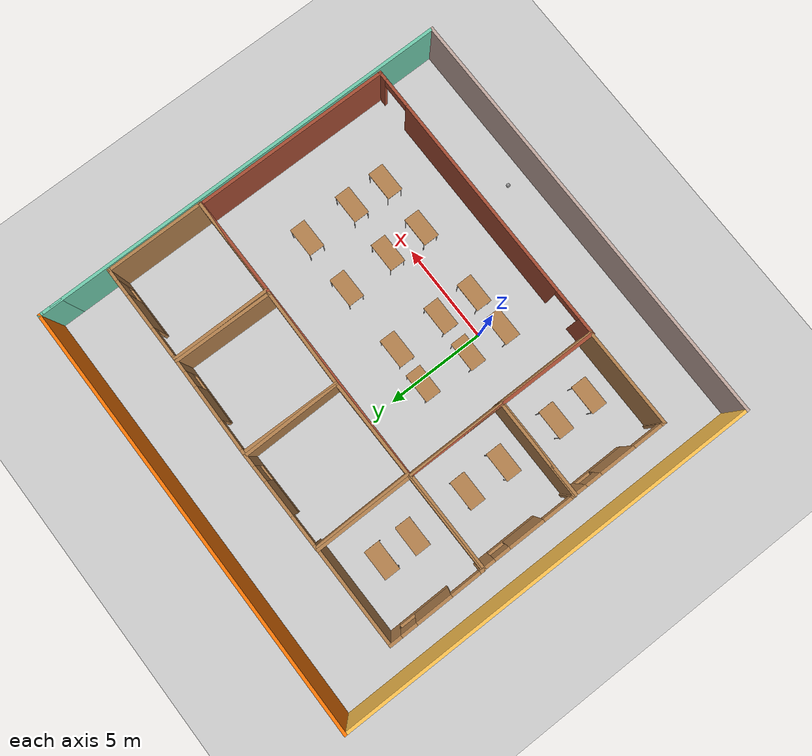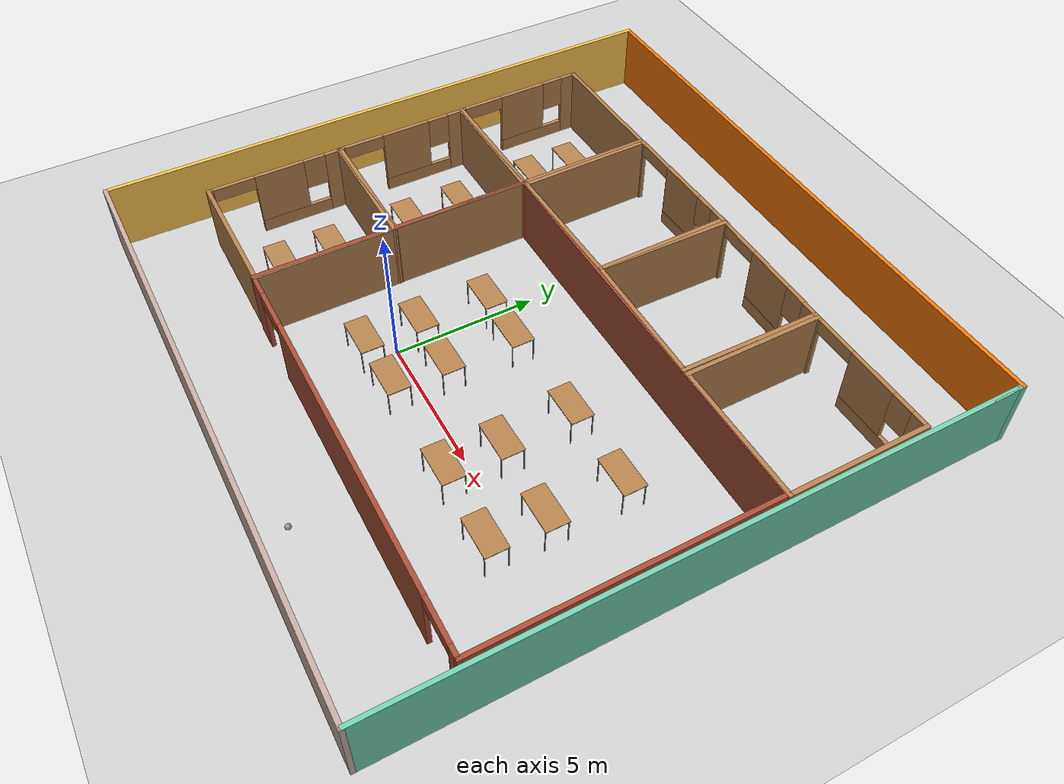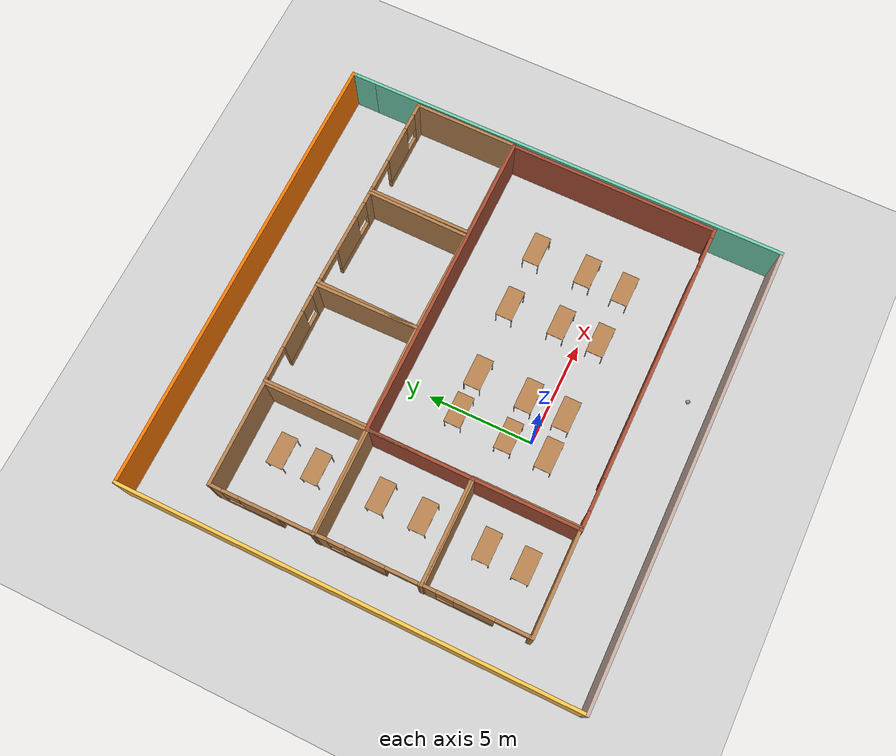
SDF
<sdf version="1.6">
 <world name="default">
  <plugin name="hello" filename="libhello.so"/>
  <model name="ground_plane">
   <static>1</static>
   <link name="link">
    <collision name="collision">
     <geometry><plane><normal>0 0 1</normal><size>100 100</size></plane></geometry>
     <surface>
      <contact><collide_bitmask>65535</collide_bitmask></contact>
      <friction><ode><mu>100</mu><mu2>50</mu2></ode></friction>
     </surface>
    </collision>
    <visual name="visual">
     <cast_shadows>0</cast_shadows>
     <geometry><plane><normal>0 0 1</normal><size>100 100</size></plane></geometry>
     <material>
      <script><uri>file://media/materials/scripts/gazebo.material</uri><name>Gazebo/Grey</name></script>
     </material>
    </visual>
   </link>
  </model>
  <gravity>0 0 -9.8</gravity>
  <magnetic_field>6e-06 2.3e-05 -4.2e-05</magnetic_field>
  <atmosphere type="adiabatic"/>
  <physics name="default_physics" default="0" type="ode">
   <max_step_size>0.001</max_step_size>
   <real_time_factor>1</real_time_factor>
   <real_time_update_rate>1000</real_time_update_rate>
  </physics>
  <scene><ambient>0.4 0.4 0.4 1</ambient><background>0.7 0.7 0.7 1</background><shadows>1</shadows></scene>
  <spherical_coordinates>
   <surface_model>EARTH_WGS84</surface_model>
   <latitude_deg>0</latitude_deg>
   <longitude_deg>0</longitude_deg>
   <elevation>0</elevation>
   <heading_deg>0</heading_deg>
  </spherical_coordinates>
  <model name="classroom">
   <pose>4.37991 1.48271 0 0 -0 0</pose>
   <link name="Wall_0">
    <collision name="Wall_0_Collision">
     <geometry><box><size>10 0.15 2.5</size></box></geometry>
     <pose>0 0 1.25 0 -0 0</pose>
    </collision>
    <visual name="Wall_0_Visual">
     <pose>0 0 1.25 0 -0 0</pose>
     <geometry><box><size>10 0.15 2.5</size></box></geometry>
     <material>
      <script><uri>file://media/materials/scripts/gazebo.material</uri><name>Gazebo/Bricks</name></script>
      <ambient>1 1 1 1</ambient>
     </material>
     <meta><layer>0</layer></meta>
    </visual>
    <pose>-7.425 0 0 0 -0 1.5708</pose>
   </link>
   <link name="Wall_2">
    <collision name="Wall_2_Collision">
     <geometry><box><size>15 0.15 2.5</size></box></geometry>
     <pose>0 0 1.25 0 -0 0</pose>
    </collision>
    <visual name="Wall_2_Visual">
     <pose>0 0 1.25 0 -0 0</pose>
     <geometry><box><size>15 0.15 2.5</size></box></geometry>
     <material>
      <script><uri>file://media/materials/scripts/gazebo.material</uri><name>Gazebo/Bricks</name></script>
      <ambient>1 1 1 1</ambient>
     </material>
     <meta><layer>0</layer></meta>
    </visual>
    <pose>0 4.925 0 0 -0 0</pose>
   </link>
   <link name="Wall_4">
    <collision name="Wall_4_Collision">
     <geometry><box><size>10 0.15 2.5</size></box></geometry>
     <pose>0 0 1.25 0 -0 0</pose>
    </collision>
    <visual name="Wall_4_Visual">
     <pose>0 0 1.25 0 -0 0</pose>
     <geometry><box><size>10 0.15 2.5</size></box></geometry>
     <material>
      <script><uri>file://media/materials/scripts/gazebo.material</uri><name>Gazebo/Bricks</name></script>
      <ambient>1 1 1 1</ambient>
     </material>
     <meta><layer>0</layer></meta>
    </visual>
    <pose>7.425 0 0 0 0 -1.5708</pose>
   </link>
   <link name="Wall_6">
    <pose>0 -4.925 0 0 -0 0</pose>
    <visual name="Wall_6_Visual_0">
     <pose>-7.03429 0 1.25 0 -0 0</pose>
     <geometry><box><size>0.931421 0.15 2.5</size></box></geometry>
     <material>
      <script><uri>file://media/materials/scripts/gazebo.material</uri><name>Gazebo/Bricks</name></script>
      <ambient>1 1 1 1</ambient>
     </material>
     <meta><layer>0</layer></meta>
    </visual>
    <collision name="Wall_6_Collision_0">
     <geometry><box><size>0.931421 0.15 2.5</size></box></geometry>
     <pose>-7.03429 0 1.25 0 -0 0</pose>
    </collision>
    <visual name="Wall_6_Visual_1">
     <pose>0.218509 0 1.25 0 -0 0</pose>
     <geometry><box><size>10.5742 0.15 2.5</size></box></geometry>
     <material>
      <script><uri>file://media/materials/scripts/gazebo.material</uri><name>Gazebo/Bricks</name></script>
      <ambient>1 1 1 1</ambient>
     </material>
     <meta><layer>0</layer></meta>
    </visual>
    <collision name="Wall_6_Collision_1">
     <geometry><box><size>10.5742 0.15 2.5</size></box></geometry>
     <pose>0.218509 0 1.25 0 -0 0</pose>
    </collision>
    <visual name="Wall_6_Visual_2">
     <pose>7.2528 0 1.25 0 -0 0</pose>
     <geometry><box><size>0.494402 0.15 2.5</size></box></geometry>
     <material>
      <script><uri>file://media/materials/scripts/gazebo.material</uri><name>Gazebo/Bricks</name></script>
      <ambient>1 1 1 1</ambient>
     </material>
     <meta><layer>0</layer></meta>
    </visual>
    <collision name="Wall_6_Collision_2">
     <geometry><box><size>0.494402 0.15 2.5</size></box></geometry>
     <pose>7.2528 0 1.25 0 -0 0</pose>
    </collision>
    <visual name="Wall_6_Visual_3">
     <pose>-5.81858 0 2.25 0 -0 0</pose>
     <geometry><box><size>1.5 0.15 0.5</size></box></geometry>
     <material>
      <script><uri>file://media/materials/scripts/gazebo.material</uri><name>Gazebo/Bricks</name></script>
      <ambient>1 1 1 1</ambient>
     </material>
     <meta><layer>0</layer></meta>
    </visual>
    <collision name="Wall_6_Collision_3">
     <geometry><box><size>1.5 0.15 0.5</size></box></geometry>
     <pose>-5.81858 0 2.25 0 -0 0</pose>
    </collision>
    <visual name="Wall_6_Visual_4">
     <pose>6.2556 0 2.25 0 -0 0</pose>
     <geometry><box><size>1.5 0.15 0.5</size></box></geometry>
     <material>
      <script><uri>file://media/materials/scripts/gazebo.material</uri><name>Gazebo/Bricks</name></script>
      <ambient>1 1 1 1</ambient>
     </material>
     <meta><layer>0</layer></meta>
    </visual>
    <collision name="Wall_6_Collision_4">
     <geometry><box><size>1.5 0.15 0.5</size></box></geometry>
     <pose>6.2556 0 2.25 0 -0 0</pose>
    </collision>
   </link>
   <static>1</static>
  </model>
  <model name="studio">
   <pose>9.41356 8.87492 0 0 -0 3.14131</pose>
   <link name="Wall_10">
    <collision name="Wall_10_Collision">
     <geometry><box><size>5 0.15 2.5</size></box></geometry>
     <pose>0 0 1.25 0 -0 0</pose>
    </collision>
    <visual name="Wall_10_Visual">
     <pose>0 0 1.25 0 -0 0</pose>
     <geometry><box><size>5 0.15 2.5</size></box></geometry>
     <material>
      <script><uri>file://media/materials/scripts/gazebo.material</uri><name>Gazebo/Wood</name></script>
      <ambient>1 1 1 1</ambient>
     </material>
     <meta><layer>0</layer></meta>
    </visual>
    <pose>0 2.42482 0 0 0 -7.3e-05</pose>
   </link>
   <link name="Wall_13">
    <collision name="Wall_13_Collision">
     <geometry><box><size>5 0.15 2.5</size></box></geometry>
     <pose>0 0 1.25 0 -0 0</pose>
    </collision>
    <visual name="Wall_13_Visual">
     <pose>0 0 1.25 0 -0 0</pose>
     <geometry><box><size>5 0.15 2.5</size></box></geometry>
     <material>
      <script><uri>file://media/materials/scripts/gazebo.material</uri><name>Gazebo/Wood</name></script>
      <ambient>1 1 1 1</ambient>
     </material>
     <meta><layer>0</layer></meta>
    </visual>
    <pose>-2.42502 -3e-06 0 0 0 -1.5708</pose>
   </link>
   <link name="Wall_15">
    <pose>-2e-05 -2.425 0 0 -0 0</pose>
    <visual name="Wall_15_Visual_0">
     <pose>-2.17395 0 1.25 0 -0 0</pose>
     <geometry><box><size>0.652095 0.15 2.5</size></box></geometry>
     <material>
      <script><uri>file://media/materials/scripts/gazebo.material</uri><name>Gazebo/Wood</name></script>
      <ambient>1 1 1 1</ambient>
     </material>
     <meta><layer>0</layer></meta>
    </visual>
    <collision name="Wall_15_Collision_0">
     <geometry><box><size>0.652095 0.15 2.5</size></box></geometry>
     <pose>-2.17395 0 1.25 0 -0 0</pose>
    </collision>
    <visual name="Wall_15_Visual_1">
     <pose>2.38574 0 1.25 0 -0 0</pose>
     <geometry><box><size>0.228515 0.15 2.5</size></box></geometry>
     <material>
      <script><uri>file://media/materials/scripts/gazebo.material</uri><name>Gazebo/Wood</name></script>
      <ambient>1 1 1 1</ambient>
     </material>
     <meta><layer>0</layer></meta>
    </visual>
    <collision name="Wall_15_Collision_1">
     <geometry><box><size>0.228515 0.15 2.5</size></box></geometry>
     <pose>2.38574 0 1.25 0 -0 0</pose>
    </collision>
    <visual name="Wall_15_Visual_2">
     <pose>-0.53821 0 0.25 0 -0 0</pose>
     <geometry><box><size>2.61939 0.15 0.5</size></box></geometry>
     <material>
      <script><uri>file://media/materials/scripts/gazebo.material</uri><name>Gazebo/Wood</name></script>
      <ambient>1 1 1 1</ambient>
     </material>
     <meta><layer>0</layer></meta>
    </visual>
    <collision name="Wall_15_Collision_2">
     <geometry><box><size>2.61939 0.15 0.5</size></box></geometry>
     <pose>-0.53821 0 0.25 0 -0 0</pose>
    </collision>
    <visual name="Wall_15_Visual_3">
     <pose>-0.13821 0 1.5 0 -0 0</pose>
     <geometry><box><size>1.81939 0.15 2</size></box></geometry>
     <material>
      <script><uri>file://media/materials/scripts/gazebo.material</uri><name>Gazebo/Wood</name></script>
      <ambient>1 1 1 1</ambient>
     </material>
     <meta><layer>0</layer></meta>
    </visual>
    <collision name="Wall_15_Collision_3">
     <geometry><box><size>1.81939 0.15 2</size></box></geometry>
     <pose>-0.13821 0 1.5 0 -0 0</pose>
    </collision>
    <visual name="Wall_15_Visual_4">
     <pose>-1.4479 0 1.9 0 -0 0</pose>
     <geometry><box><size>0.8 0.15 1.2</size></box></geometry>
     <material>
      <script><uri>file://media/materials/scripts/gazebo.material</uri><name>Gazebo/Wood</name></script>
      <ambient>1 1 1 1</ambient>
     </material>
     <meta><layer>0</layer></meta>
    </visual>
    <collision name="Wall_15_Collision_4">
     <geometry><box><size>0.8 0.15 1.2</size></box></geometry>
     <pose>-1.4479 0 1.9 0 -0 0</pose>
    </collision>
    <visual name="Wall_15_Visual_5">
     <pose>1.52148 0 2.25 0 -0 0</pose>
     <geometry><box><size>1.5 0.15 0.5</size></box></geometry>
     <material>
      <script><uri>file://media/materials/scripts/gazebo.material</uri><name>Gazebo/Wood</name></script>
      <ambient>1 1 1 1</ambient>
     </material>
     <meta><layer>0</layer></meta>
    </visual>
    <collision name="Wall_15_Collision_5">
     <geometry><box><size>1.5 0.15 0.5</size></box></geometry>
     <pose>1.52148 0 2.25 0 -0 0</pose>
    </collision>
   </link>
   <link name="Wall_16">
    <collision name="Wall_16_Collision">
     <geometry><box><size>4.99965 0.15 2.5</size></box></geometry>
     <pose>0 0 1.25 0 -0 0</pose>
    </collision>
    <visual name="Wall_16_Visual">
     <pose>0 0 1.25 0 -0 0</pose>
     <geometry><box><size>4.99965 0.15 2.5</size></box></geometry>
     <material>
      <script><uri>file://media/materials/scripts/gazebo.material</uri><name>Gazebo/Wood</name></script>
      <ambient>1 1 1 1</ambient>
     </material>
     <meta><layer>0</layer></meta>
    </visual>
    <pose>2.425 -0.00018 0 0 -0 1.57079</pose>
   </link>
   <static>1</static>
  </model>
  <model name="studio_0">
   <pose>4.40677 8.90584 0 0 -0 3.12886</pose>
   <link name="Wall_10">
    <collision name="Wall_10_Collision">
     <geometry><box><size>5 0.15 2.5</size></box></geometry>
     <pose>0 0 1.25 0 -0 0</pose>
    </collision>
    <visual name="Wall_10_Visual">
     <pose>0 0 1.25 0 -0 0</pose>
     <geometry><box><size>5 0.15 2.5</size></box></geometry>
     <material>
      <script><uri>file://media/materials/scripts/gazebo.material</uri><name>Gazebo/Wood</name></script>
      <ambient>1 1 1 1</ambient>
     </material>
     <meta><layer>0</layer></meta>
    </visual>
    <pose>0 2.42482 0 0 0 -7.3e-05</pose>
   </link>
   <link name="Wall_13">
    <collision name="Wall_13_Collision">
     <geometry><box><size>5 0.15 2.5</size></box></geometry>
     <pose>0 0 1.25 0 -0 0</pose>
    </collision>
    <visual name="Wall_13_Visual">
     <pose>0 0 1.25 0 -0 0</pose>
     <geometry><box><size>5 0.15 2.5</size></box></geometry>
     <material>
      <script><uri>file://media/materials/scripts/gazebo.material</uri><name>Gazebo/Wood</name></script>
      <ambient>1 1 1 1</ambient>
     </material>
     <meta><layer>0</layer></meta>
    </visual>
    <pose>-2.42502 -3e-06 0 0 0 -1.5708</pose>
   </link>
   <link name="Wall_15">
    <pose>-2e-05 -2.425 0 0 -0 0</pose>
    <visual name="Wall_15_Visual_0">
     <pose>-2.17395 0 1.25 0 -0 0</pose>
     <geometry><box><size>0.652095 0.15 2.5</size></box></geometry>
     <material>
      <script><uri>file://media/materials/scripts/gazebo.material</uri><name>Gazebo/Wood</name></script>
      <ambient>1 1 1 1</ambient>
     </material>
     <meta><layer>0</layer></meta>
    </visual>
    <collision name="Wall_15_Collision_0">
     <geometry><box><size>0.652095 0.15 2.5</size></box></geometry>
     <pose>-2.17395 0 1.25 0 -0 0</pose>
    </collision>
    <visual name="Wall_15_Visual_1">
     <pose>2.38574 0 1.25 0 -0 0</pose>
     <geometry><box><size>0.228515 0.15 2.5</size></box></geometry>
     <material>
      <script><uri>file://media/materials/scripts/gazebo.material</uri><name>Gazebo/Wood</name></script>
      <ambient>1 1 1 1</ambient>
     </material>
     <meta><layer>0</layer></meta>
    </visual>
    <collision name="Wall_15_Collision_1">
     <geometry><box><size>0.228515 0.15 2.5</size></box></geometry>
     <pose>2.38574 0 1.25 0 -0 0</pose>
    </collision>
    <visual name="Wall_15_Visual_2">
     <pose>-0.53821 0 0.25 0 -0 0</pose>
     <geometry><box><size>2.61939 0.15 0.5</size></box></geometry>
     <material>
      <script><uri>file://media/materials/scripts/gazebo.material</uri><name>Gazebo/Wood</name></script>
      <ambient>1 1 1 1</ambient>
     </material>
     <meta><layer>0</layer></meta>
    </visual>
    <collision name="Wall_15_Collision_2">
     <geometry><box><size>2.61939 0.15 0.5</size></box></geometry>
     <pose>-0.53821 0 0.25 0 -0 0</pose>
    </collision>
    <visual name="Wall_15_Visual_3">
     <pose>-0.13821 0 1.5 0 -0 0</pose>
     <geometry><box><size>1.81939 0.15 2</size></box></geometry>
     <material>
      <script><uri>file://media/materials/scripts/gazebo.material</uri><name>Gazebo/Wood</name></script>
      <ambient>1 1 1 1</ambient>
     </material>
     <meta><layer>0</layer></meta>
    </visual>
    <collision name="Wall_15_Collision_3">
     <geometry><box><size>1.81939 0.15 2</size></box></geometry>
     <pose>-0.13821 0 1.5 0 -0 0</pose>
    </collision>
    <visual name="Wall_15_Visual_4">
     <pose>-1.4479 0 1.9 0 -0 0</pose>
     <geometry><box><size>0.8 0.15 1.2</size></box></geometry>
     <material>
      <script><uri>file://media/materials/scripts/gazebo.material</uri><name>Gazebo/Wood</name></script>
      <ambient>1 1 1 1</ambient>
     </material>
     <meta><layer>0</layer></meta>
    </visual>
    <collision name="Wall_15_Collision_4">
     <geometry><box><size>0.8 0.15 1.2</size></box></geometry>
     <pose>-1.4479 0 1.9 0 -0 0</pose>
    </collision>
    <visual name="Wall_15_Visual_5">
     <pose>1.52148 0 2.25 0 -0 0</pose>
     <geometry><box><size>1.5 0.15 0.5</size></box></geometry>
     <material>
      <script><uri>file://media/materials/scripts/gazebo.material</uri><name>Gazebo/Wood</name></script>
      <ambient>1 1 1 1</ambient>
     </material>
     <meta><layer>0</layer></meta>
    </visual>
    <collision name="Wall_15_Collision_5">
     <geometry><box><size>1.5 0.15 0.5</size></box></geometry>
     <pose>1.52148 0 2.25 0 -0 0</pose>
    </collision>
   </link>
   <link name="Wall_16">
    <collision name="Wall_16_Collision">
     <geometry><box><size>4.99965 0.15 2.5</size></box></geometry>
     <pose>0 0 1.25 0 -0 0</pose>
    </collision>
    <visual name="Wall_16_Visual">
     <pose>0 0 1.25 0 -0 0</pose>
     <geometry><box><size>4.99965 0.15 2.5</size></box></geometry>
     <material>
      <script><uri>file://media/materials/scripts/gazebo.material</uri><name>Gazebo/Wood</name></script>
      <ambient>1 1 1 1</ambient>
     </material>
     <meta><layer>0</layer></meta>
    </visual>
    <pose>2.425 -0.00018 0 0 -0 1.57079</pose>
   </link>
   <static>1</static>
  </model>
  <model name="studio_1">
   <pose>-0.535475 8.90662 0 0 0 -3.12868</pose>
   <link name="Wall_10">
    <collision name="Wall_10_Collision">
     <geometry><box><size>5 0.15 2.5</size></box></geometry>
     <pose>0 0 1.25 0 -0 0</pose>
    </collision>
    <visual name="Wall_10_Visual">
     <pose>0 0 1.25 0 -0 0</pose>
     <geometry><box><size>5 0.15 2.5</size></box></geometry>
     <material>
      <script><uri>file://media/materials/scripts/gazebo.material</uri><name>Gazebo/Wood</name></script>
      <ambient>1 1 1 1</ambient>
     </material>
     <meta><layer>0</layer></meta>
    </visual>
    <pose>0 2.42482 0 0 0 -7.3e-05</pose>
   </link>
   <link name="Wall_13">
    <collision name="Wall_13_Collision">
     <geometry><box><size>5 0.15 2.5</size></box></geometry>
     <pose>0 0 1.25 0 -0 0</pose>
    </collision>
    <visual name="Wall_13_Visual">
     <pose>0 0 1.25 0 -0 0</pose>
     <geometry><box><size>5 0.15 2.5</size></box></geometry>
     <material>
      <script><uri>file://media/materials/scripts/gazebo.material</uri><name>Gazebo/Wood</name></script>
      <ambient>1 1 1 1</ambient>
     </material>
     <meta><layer>0</layer></meta>
    </visual>
    <pose>-2.42502 -3e-06 0 0 0 -1.5708</pose>
   </link>
   <link name="Wall_15">
    <pose>-2e-05 -2.425 0 0 -0 0</pose>
    <visual name="Wall_15_Visual_0">
     <pose>-2.17395 0 1.25 0 -0 0</pose>
     <geometry><box><size>0.652095 0.15 2.5</size></box></geometry>
     <material>
      <script><uri>file://media/materials/scripts/gazebo.material</uri><name>Gazebo/Wood</name></script>
      <ambient>1 1 1 1</ambient>
     </material>
     <meta><layer>0</layer></meta>
    </visual>
    <collision name="Wall_15_Collision_0">
     <geometry><box><size>0.652095 0.15 2.5</size></box></geometry>
     <pose>-2.17395 0 1.25 0 -0 0</pose>
    </collision>
    <visual name="Wall_15_Visual_1">
     <pose>2.38574 0 1.25 0 -0 0</pose>
     <geometry><box><size>0.228515 0.15 2.5</size></box></geometry>
     <material>
      <script><uri>file://media/materials/scripts/gazebo.material</uri><name>Gazebo/Wood</name></script>
      <ambient>1 1 1 1</ambient>
     </material>
     <meta><layer>0</layer></meta>
    </visual>
    <collision name="Wall_15_Collision_1">
     <geometry><box><size>0.228515 0.15 2.5</size></box></geometry>
     <pose>2.38574 0 1.25 0 -0 0</pose>
    </collision>
    <visual name="Wall_15_Visual_2">
     <pose>-0.53821 0 0.25 0 -0 0</pose>
     <geometry><box><size>2.61939 0.15 0.5</size></box></geometry>
     <material>
      <script><uri>file://media/materials/scripts/gazebo.material</uri><name>Gazebo/Wood</name></script>
      <ambient>1 1 1 1</ambient>
     </material>
     <meta><layer>0</layer></meta>
    </visual>
    <collision name="Wall_15_Collision_2">
     <geometry><box><size>2.61939 0.15 0.5</size></box></geometry>
     <pose>-0.53821 0 0.25 0 -0 0</pose>
    </collision>
    <visual name="Wall_15_Visual_3">
     <pose>-0.13821 0 1.5 0 -0 0</pose>
     <geometry><box><size>1.81939 0.15 2</size></box></geometry>
     <material>
      <script><uri>file://media/materials/scripts/gazebo.material</uri><name>Gazebo/Wood</name></script>
      <ambient>1 1 1 1</ambient>
     </material>
     <meta><layer>0</layer></meta>
    </visual>
    <collision name="Wall_15_Collision_3">
     <geometry><box><size>1.81939 0.15 2</size></box></geometry>
     <pose>-0.13821 0 1.5 0 -0 0</pose>
    </collision>
    <visual name="Wall_15_Visual_4">
     <pose>-1.4479 0 1.9 0 -0 0</pose>
     <geometry><box><size>0.8 0.15 1.2</size></box></geometry>
     <material>
      <script><uri>file://media/materials/scripts/gazebo.material</uri><name>Gazebo/Wood</name></script>
      <ambient>1 1 1 1</ambient>
     </material>
     <meta><layer>0</layer></meta>
    </visual>
    <collision name="Wall_15_Collision_4">
     <geometry><box><size>0.8 0.15 1.2</size></box></geometry>
     <pose>-1.4479 0 1.9 0 -0 0</pose>
    </collision>
    <visual name="Wall_15_Visual_5">
     <pose>1.52148 0 2.25 0 -0 0</pose>
     <geometry><box><size>1.5 0.15 0.5</size></box></geometry>
     <material>
      <script><uri>file://media/materials/scripts/gazebo.material</uri><name>Gazebo/Wood</name></script>
      <ambient>1 1 1 1</ambient>
     </material>
     <meta><layer>0</layer></meta>
    </visual>
    <collision name="Wall_15_Collision_5">
     <geometry><box><size>1.5 0.15 0.5</size></box></geometry>
     <pose>1.52148 0 2.25 0 -0 0</pose>
    </collision>
   </link>
   <link name="Wall_16">
    <collision name="Wall_16_Collision">
     <geometry><box><size>4.99965 0.15 2.5</size></box></geometry>
     <pose>0 0 1.25 0 -0 0</pose>
    </collision>
    <visual name="Wall_16_Visual">
     <pose>0 0 1.25 0 -0 0</pose>
     <geometry><box><size>4.99965 0.15 2.5</size></box></geometry>
     <material>
      <script><uri>file://media/materials/scripts/gazebo.material</uri><name>Gazebo/Wood</name></script>
      <ambient>1 1 1 1</ambient>
     </material>
     <meta><layer>0</layer></meta>
    </visual>
    <pose>2.425 -0.00018 0 0 -0 1.57079</pose>
   </link>
   <static>1</static>
  </model>
  <model name="table_9">
   <static>1</static>
   <link name="link">
    <collision name="surface">
     <pose>0 0 1 0 -0 0</pose>
     <geometry><box><size>1.5 0.8 0.03</size></box></geometry>
     <surface><friction><ode><mu>0.6</mu><mu2>0.6</mu2></ode></friction></surface>
    </collision>
    <visual name="visual1">
     <pose>0 0 1 0 -0 0</pose>
     <geometry><box><size>1.5 0.8 0.03</size></box></geometry>
     <material>
      <script><uri>file://media/materials/scripts/gazebo.material</uri><name>Gazebo/Wood</name></script>
     </material>
    </visual>
    <collision name="front_left_leg">
     <pose>0.68 0.38 0.5 0 -0 0</pose>
     <geometry><cylinder><radius>0.02</radius><length>1</length></cylinder></geometry>
    </collision>
    <visual name="front_left_leg">
     <pose>0.68 0.38 0.5 0 -0 0</pose>
     <geometry><cylinder><radius>0.02</radius><length>1</length></cylinder></geometry>
     <material>
      <script><uri>file://media/materials/scripts/gazebo.material</uri><name>Gazebo/Grey</name></script>
     </material>
    </visual>
    <collision name="front_right_leg">
     <pose>0.68 -0.38 0.5 0 -0 0</pose>
     <geometry><cylinder><radius>0.02</radius><length>1</length></cylinder></geometry>
    </collision>
    <visual name="front_right_leg">
     <pose>0.68 -0.38 0.5 0 -0 0</pose>
     <geometry><cylinder><radius>0.02</radius><length>1</length></cylinder></geometry>
     <material>
      <script><uri>file://media/materials/scripts/gazebo.material</uri><name>Gazebo/Grey</name></script>
     </material>
    </visual>
    <collision name="back_right_leg">
     <pose>-0.68 -0.38 0.5 0 -0 0</pose>
     <geometry><cylinder><radius>0.02</radius><length>1</length></cylinder></geometry>
    </collision>
    <visual name="back_right_leg">
     <pose>-0.68 -0.38 0.5 0 -0 0</pose>
     <geometry><cylinder><radius>0.02</radius><length>1</length></cylinder></geometry>
     <material>
      <script><uri>file://media/materials/scripts/gazebo.material</uri><name>Gazebo/Grey</name></script>
     </material>
    </visual>
    <collision name="back_left_leg">
     <pose>-0.68 0.38 0.5 0 -0 0</pose>
     <geometry><cylinder><radius>0.02</radius><length>1</length></cylinder></geometry>
    </collision>
    <visual name="back_left_leg">
     <pose>-0.68 0.38 0.5 0 -0 0</pose>
     <geometry><cylinder><radius>0.02</radius><length>1</length></cylinder></geometry>
     <material>
      <script><uri>file://media/materials/scripts/gazebo.material</uri><name>Gazebo/Grey</name></script>
     </material>
    </visual>
   </link>
   <pose>8.12729 -0.872855 0 0 -0 0</pose>
  </model>
  <model name="table_10">
   <static>1</static>
   <link name="link">
    <collision name="surface">
     <pose>0 0 1 0 -0 0</pose>
     <geometry><box><size>1.5 0.8 0.03</size></box></geometry>
     <surface><friction><ode><mu>0.6</mu><mu2>0.6</mu2></ode></friction></surface>
    </collision>
    <visual name="visual1">
     <pose>0 0 1 0 -0 0</pose>
     <geometry><box><size>1.5 0.8 0.03</size></box></geometry>
     <material>
      <script><uri>file://media/materials/scripts/gazebo.material</uri><name>Gazebo/Wood</name></script>
     </material>
    </visual>
    <collision name="front_left_leg">
     <pose>0.68 0.38 0.5 0 -0 0</pose>
     <geometry><cylinder><radius>0.02</radius><length>1</length></cylinder></geometry>
    </collision>
    <visual name="front_left_leg">
     <pose>0.68 0.38 0.5 0 -0 0</pose>
     <geometry><cylinder><radius>0.02</radius><length>1</length></cylinder></geometry>
     <material>
      <script><uri>file://media/materials/scripts/gazebo.material</uri><name>Gazebo/Grey</name></script>
     </material>
    </visual>
    <collision name="front_right_leg">
     <pose>0.68 -0.38 0.5 0 -0 0</pose>
     <geometry><cylinder><radius>0.02</radius><length>1</length></cylinder></geometry>
    </collision>
    <visual name="front_right_leg">
     <pose>0.68 -0.38 0.5 0 -0 0</pose>
     <geometry><cylinder><radius>0.02</radius><length>1</length></cylinder></geometry>
     <material>
      <script><uri>file://media/materials/scripts/gazebo.material</uri><name>Gazebo/Grey</name></script>
     </material>
    </visual>
    <collision name="back_right_leg">
     <pose>-0.68 -0.38 0.5 0 -0 0</pose>
     <geometry><cylinder><radius>0.02</radius><length>1</length></cylinder></geometry>
    </collision>
    <visual name="back_right_leg">
     <pose>-0.68 -0.38 0.5 0 -0 0</pose>
     <geometry><cylinder><radius>0.02</radius><length>1</length></cylinder></geometry>
     <material>
      <script><uri>file://media/materials/scripts/gazebo.material</uri><name>Gazebo/Grey</name></script>
     </material>
    </visual>
    <collision name="back_left_leg">
     <pose>-0.68 0.38 0.5 0 -0 0</pose>
     <geometry><cylinder><radius>0.02</radius><length>1</length></cylinder></geometry>
    </collision>
    <visual name="back_left_leg">
     <pose>-0.68 0.38 0.5 0 -0 0</pose>
     <geometry><cylinder><radius>0.02</radius><length>1</length></cylinder></geometry>
     <material>
      <script><uri>file://media/materials/scripts/gazebo.material</uri><name>Gazebo/Grey</name></script>
     </material>
    </visual>
   </link>
   <pose>8.2006 0.992468 0 0 -0 0</pose>
  </model>
  <model name="table_11">
   <static>1</static>
   <link name="link">
    <collision name="surface">
     <pose>0 0 1 0 -0 0</pose>
     <geometry><box><size>1.5 0.8 0.03</size></box></geometry>
     <surface><friction><ode><mu>0.6</mu><mu2>0.6</mu2></ode></friction></surface>
    </collision>
    <visual name="visual1">
     <pose>0 0 1 0 -0 0</pose>
     <geometry><box><size>1.5 0.8 0.03</size></box></geometry>
     <material>
      <script><uri>file://media/materials/scripts/gazebo.material</uri><name>Gazebo/Wood</name></script>
     </material>
    </visual>
    <collision name="front_left_leg">
     <pose>0.68 0.38 0.5 0 -0 0</pose>
     <geometry><cylinder><radius>0.02</radius><length>1</length></cylinder></geometry>
    </collision>
    <visual name="front_left_leg">
     <pose>0.68 0.38 0.5 0 -0 0</pose>
     <geometry><cylinder><radius>0.02</radius><length>1</length></cylinder></geometry>
     <material>
      <script><uri>file://media/materials/scripts/gazebo.material</uri><name>Gazebo/Grey</name></script>
     </material>
    </visual>
    <collision name="front_right_leg">
     <pose>0.68 -0.38 0.5 0 -0 0</pose>
     <geometry><cylinder><radius>0.02</radius><length>1</length></cylinder></geometry>
    </collision>
    <visual name="front_right_leg">
     <pose>0.68 -0.38 0.5 0 -0 0</pose>
     <geometry><cylinder><radius>0.02</radius><length>1</length></cylinder></geometry>
     <material>
      <script><uri>file://media/materials/scripts/gazebo.material</uri><name>Gazebo/Grey</name></script>
     </material>
    </visual>
    <collision name="back_right_leg">
     <pose>-0.68 -0.38 0.5 0 -0 0</pose>
     <geometry><cylinder><radius>0.02</radius><length>1</length></cylinder></geometry>
    </collision>
    <visual name="back_right_leg">
     <pose>-0.68 -0.38 0.5 0 -0 0</pose>
     <geometry><cylinder><radius>0.02</radius><length>1</length></cylinder></geometry>
     <material>
      <script><uri>file://media/materials/scripts/gazebo.material</uri><name>Gazebo/Grey</name></script>
     </material>
    </visual>
    <collision name="back_left_leg">
     <pose>-0.68 0.38 0.5 0 -0 0</pose>
     <geometry><cylinder><radius>0.02</radius><length>1</length></cylinder></geometry>
    </collision>
    <visual name="back_left_leg">
     <pose>-0.68 0.38 0.5 0 -0 0</pose>
     <geometry><cylinder><radius>0.02</radius><length>1</length></cylinder></geometry>
     <material>
      <script><uri>file://media/materials/scripts/gazebo.material</uri><name>Gazebo/Grey</name></script>
     </material>
    </visual>
   </link>
   <pose>8.2006 3.53979 0 0 -0 0</pose>
  </model>
  <model name="table_13">
   <static>1</static>
   <link name="link">
    <collision name="surface">
     <pose>0 0 1 0 -0 0</pose>
     <geometry><box><size>1.5 0.8 0.03</size></box></geometry>
     <surface><friction><ode><mu>0.6</mu><mu2>0.6</mu2></ode></friction></surface>
    </collision>
    <visual name="visual1">
     <pose>0 0 1 0 -0 0</pose>
     <geometry><box><size>1.5 0.8 0.03</size></box></geometry>
     <material>
      <script><uri>file://media/materials/scripts/gazebo.material</uri><name>Gazebo/Wood</name></script>
     </material>
    </visual>
    <collision name="front_left_leg">
     <pose>0.68 0.38 0.5 0 -0 0</pose>
     <geometry><cylinder><radius>0.02</radius><length>1</length></cylinder></geometry>
    </collision>
    <visual name="front_left_leg">
     <pose>0.68 0.38 0.5 0 -0 0</pose>
     <geometry><cylinder><radius>0.02</radius><length>1</length></cylinder></geometry>
     <material>
      <script><uri>file://media/materials/scripts/gazebo.material</uri><name>Gazebo/Grey</name></script>
     </material>
    </visual>
    <collision name="front_right_leg">
     <pose>0.68 -0.38 0.5 0 -0 0</pose>
     <geometry><cylinder><radius>0.02</radius><length>1</length></cylinder></geometry>
    </collision>
    <visual name="front_right_leg">
     <pose>0.68 -0.38 0.5 0 -0 0</pose>
     <geometry><cylinder><radius>0.02</radius><length>1</length></cylinder></geometry>
     <material>
      <script><uri>file://media/materials/scripts/gazebo.material</uri><name>Gazebo/Grey</name></script>
     </material>
    </visual>
    <collision name="back_right_leg">
     <pose>-0.68 -0.38 0.5 0 -0 0</pose>
     <geometry><cylinder><radius>0.02</radius><length>1</length></cylinder></geometry>
    </collision>
    <visual name="back_right_leg">
     <pose>-0.68 -0.38 0.5 0 -0 0</pose>
     <geometry><cylinder><radius>0.02</radius><length>1</length></cylinder></geometry>
     <material>
      <script><uri>file://media/materials/scripts/gazebo.material</uri><name>Gazebo/Grey</name></script>
     </material>
    </visual>
    <collision name="back_left_leg">
     <pose>-0.68 0.38 0.5 0 -0 0</pose>
     <geometry><cylinder><radius>0.02</radius><length>1</length></cylinder></geometry>
    </collision>
    <visual name="back_left_leg">
     <pose>-0.68 0.38 0.5 0 -0 0</pose>
     <geometry><cylinder><radius>0.02</radius><length>1</length></cylinder></geometry>
     <material>
      <script><uri>file://media/materials/scripts/gazebo.material</uri><name>Gazebo/Grey</name></script>
     </material>
    </visual>
   </link>
   <pose>5.41488 -0.850729 0 0 -0 0</pose>
  </model>
  <model name="table_14">
   <static>1</static>
   <link name="link">
    <collision name="surface">
     <pose>0 0 1 0 -0 0</pose>
     <geometry><box><size>1.5 0.8 0.03</size></box></geometry>
     <surface><friction><ode><mu>0.6</mu><mu2>0.6</mu2></ode></friction></surface>
    </collision>
    <visual name="visual1">
     <pose>0 0 1 0 -0 0</pose>
     <geometry><box><size>1.5 0.8 0.03</size></box></geometry>
     <material>
      <script><uri>file://media/materials/scripts/gazebo.material</uri><name>Gazebo/Wood</name></script>
     </material>
    </visual>
    <collision name="front_left_leg">
     <pose>0.68 0.38 0.5 0 -0 0</pose>
     <geometry><cylinder><radius>0.02</radius><length>1</length></cylinder></geometry>
    </collision>
    <visual name="front_left_leg">
     <pose>0.68 0.38 0.5 0 -0 0</pose>
     <geometry><cylinder><radius>0.02</radius><length>1</length></cylinder></geometry>
     <material>
      <script><uri>file://media/materials/scripts/gazebo.material</uri><name>Gazebo/Grey</name></script>
     </material>
    </visual>
    <collision name="front_right_leg">
     <pose>0.68 -0.38 0.5 0 -0 0</pose>
     <geometry><cylinder><radius>0.02</radius><length>1</length></cylinder></geometry>
    </collision>
    <visual name="front_right_leg">
     <pose>0.68 -0.38 0.5 0 -0 0</pose>
     <geometry><cylinder><radius>0.02</radius><length>1</length></cylinder></geometry>
     <material>
      <script><uri>file://media/materials/scripts/gazebo.material</uri><name>Gazebo/Grey</name></script>
     </material>
    </visual>
    <collision name="back_right_leg">
     <pose>-0.68 -0.38 0.5 0 -0 0</pose>
     <geometry><cylinder><radius>0.02</radius><length>1</length></cylinder></geometry>
    </collision>
    <visual name="back_right_leg">
     <pose>-0.68 -0.38 0.5 0 -0 0</pose>
     <geometry><cylinder><radius>0.02</radius><length>1</length></cylinder></geometry>
     <material>
      <script><uri>file://media/materials/scripts/gazebo.material</uri><name>Gazebo/Grey</name></script>
     </material>
    </visual>
    <collision name="back_left_leg">
     <pose>-0.68 0.38 0.5 0 -0 0</pose>
     <geometry><cylinder><radius>0.02</radius><length>1</length></cylinder></geometry>
    </collision>
    <visual name="back_left_leg">
     <pose>-0.68 0.38 0.5 0 -0 0</pose>
     <geometry><cylinder><radius>0.02</radius><length>1</length></cylinder></geometry>
     <material>
      <script><uri>file://media/materials/scripts/gazebo.material</uri><name>Gazebo/Grey</name></script>
     </material>
    </visual>
   </link>
   <pose>5.41488 1.07261 0 0 -0 0</pose>
  </model>
  <model name="table_15">
   <static>1</static>
   <link name="link">
    <collision name="surface">
     <pose>0 0 1 0 -0 0</pose>
     <geometry><box><size>1.5 0.8 0.03</size></box></geometry>
     <surface><friction><ode><mu>0.6</mu><mu2>0.6</mu2></ode></friction></surface>
    </collision>
    <visual name="visual1">
     <pose>0 0 1 0 -0 0</pose>
     <geometry><box><size>1.5 0.8 0.03</size></box></geometry>
     <material>
      <script><uri>file://media/materials/scripts/gazebo.material</uri><name>Gazebo/Wood</name></script>
     </material>
    </visual>
    <collision name="front_left_leg">
     <pose>0.68 0.38 0.5 0 -0 0</pose>
     <geometry><cylinder><radius>0.02</radius><length>1</length></cylinder></geometry>
    </collision>
    <visual name="front_left_leg">
     <pose>0.68 0.38 0.5 0 -0 0</pose>
     <geometry><cylinder><radius>0.02</radius><length>1</length></cylinder></geometry>
     <material>
      <script><uri>file://media/materials/scripts/gazebo.material</uri><name>Gazebo/Grey</name></script>
     </material>
    </visual>
    <collision name="front_right_leg">
     <pose>0.68 -0.38 0.5 0 -0 0</pose>
     <geometry><cylinder><radius>0.02</radius><length>1</length></cylinder></geometry>
    </collision>
    <visual name="front_right_leg">
     <pose>0.68 -0.38 0.5 0 -0 0</pose>
     <geometry><cylinder><radius>0.02</radius><length>1</length></cylinder></geometry>
     <material>
      <script><uri>file://media/materials/scripts/gazebo.material</uri><name>Gazebo/Grey</name></script>
     </material>
    </visual>
    <collision name="back_right_leg">
     <pose>-0.68 -0.38 0.5 0 -0 0</pose>
     <geometry><cylinder><radius>0.02</radius><length>1</length></cylinder></geometry>
    </collision>
    <visual name="back_right_leg">
     <pose>-0.68 -0.38 0.5 0 -0 0</pose>
     <geometry><cylinder><radius>0.02</radius><length>1</length></cylinder></geometry>
     <material>
      <script><uri>file://media/materials/scripts/gazebo.material</uri><name>Gazebo/Grey</name></script>
     </material>
    </visual>
    <collision name="back_left_leg">
     <pose>-0.68 0.38 0.5 0 -0 0</pose>
     <geometry><cylinder><radius>0.02</radius><length>1</length></cylinder></geometry>
    </collision>
    <visual name="back_left_leg">
     <pose>-0.68 0.38 0.5 0 -0 0</pose>
     <geometry><cylinder><radius>0.02</radius><length>1</length></cylinder></geometry>
     <material>
      <script><uri>file://media/materials/scripts/gazebo.material</uri><name>Gazebo/Grey</name></script>
     </material>
    </visual>
   </link>
   <pose>5.26825 3.52287 0 0 -0 0</pose>
  </model>
  <model name="table_17">
   <static>1</static>
   <link name="link">
    <collision name="surface">
     <pose>0 0 1 0 -0 0</pose>
     <geometry><box><size>1.5 0.8 0.03</size></box></geometry>
     <surface><friction><ode><mu>0.6</mu><mu2>0.6</mu2></ode></friction></surface>
    </collision>
    <visual name="visual1">
     <pose>0 0 1 0 -0 0</pose>
     <geometry><box><size>1.5 0.8 0.03</size></box></geometry>
     <material>
      <script><uri>file://media/materials/scripts/gazebo.material</uri><name>Gazebo/Wood</name></script>
     </material>
    </visual>
    <collision name="front_left_leg">
     <pose>0.68 0.38 0.5 0 -0 0</pose>
     <geometry><cylinder><radius>0.02</radius><length>1</length></cylinder></geometry>
    </collision>
    <visual name="front_left_leg">
     <pose>0.68 0.38 0.5 0 -0 0</pose>
     <geometry><cylinder><radius>0.02</radius><length>1</length></cylinder></geometry>
     <material>
      <script><uri>file://media/materials/scripts/gazebo.material</uri><name>Gazebo/Grey</name></script>
     </material>
    </visual>
    <collision name="front_right_leg">
     <pose>0.68 -0.38 0.5 0 -0 0</pose>
     <geometry><cylinder><radius>0.02</radius><length>1</length></cylinder></geometry>
    </collision>
    <visual name="front_right_leg">
     <pose>0.68 -0.38 0.5 0 -0 0</pose>
     <geometry><cylinder><radius>0.02</radius><length>1</length></cylinder></geometry>
     <material>
      <script><uri>file://media/materials/scripts/gazebo.material</uri><name>Gazebo/Grey</name></script>
     </material>
    </visual>
    <collision name="back_right_leg">
     <pose>-0.68 -0.38 0.5 0 -0 0</pose>
     <geometry><cylinder><radius>0.02</radius><length>1</length></cylinder></geometry>
    </collision>
    <visual name="back_right_leg">
     <pose>-0.68 -0.38 0.5 0 -0 0</pose>
     <geometry><cylinder><radius>0.02</radius><length>1</length></cylinder></geometry>
     <material>
      <script><uri>file://media/materials/scripts/gazebo.material</uri><name>Gazebo/Grey</name></script>
     </material>
    </visual>
    <collision name="back_left_leg">
     <pose>-0.68 0.38 0.5 0 -0 0</pose>
     <geometry><cylinder><radius>0.02</radius><length>1</length></cylinder></geometry>
    </collision>
    <visual name="back_left_leg">
     <pose>-0.68 0.38 0.5 0 -0 0</pose>
     <geometry><cylinder><radius>0.02</radius><length>1</length></cylinder></geometry>
     <material>
      <script><uri>file://media/materials/scripts/gazebo.material</uri><name>Gazebo/Grey</name></script>
     </material>
    </visual>
   </link>
   <pose>1.60277 -0.861568 0 0 -0 0</pose>
  </model>
  <model name="table_18">
   <static>1</static>
   <link name="link">
    <collision name="surface">
     <pose>0 0 1 0 -0 0</pose>
     <geometry><box><size>1.5 0.8 0.03</size></box></geometry>
     <surface><friction><ode><mu>0.6</mu><mu2>0.6</mu2></ode></friction></surface>
    </collision>
    <visual name="visual1">
     <pose>0 0 1 0 -0 0</pose>
     <geometry><box><size>1.5 0.8 0.03</size></box></geometry>
     <material>
      <script><uri>file://media/materials/scripts/gazebo.material</uri><name>Gazebo/Wood</name></script>
     </material>
    </visual>
    <collision name="front_left_leg">
     <pose>0.68 0.38 0.5 0 -0 0</pose>
     <geometry><cylinder><radius>0.02</radius><length>1</length></cylinder></geometry>
    </collision>
    <visual name="front_left_leg">
     <pose>0.68 0.38 0.5 0 -0 0</pose>
     <geometry><cylinder><radius>0.02</radius><length>1</length></cylinder></geometry>
     <material>
      <script><uri>file://media/materials/scripts/gazebo.material</uri><name>Gazebo/Grey</name></script>
     </material>
    </visual>
    <collision name="front_right_leg">
     <pose>0.68 -0.38 0.5 0 -0 0</pose>
     <geometry><cylinder><radius>0.02</radius><length>1</length></cylinder></geometry>
    </collision>
    <visual name="front_right_leg">
     <pose>0.68 -0.38 0.5 0 -0 0</pose>
     <geometry><cylinder><radius>0.02</radius><length>1</length></cylinder></geometry>
     <material>
      <script><uri>file://media/materials/scripts/gazebo.material</uri><name>Gazebo/Grey</name></script>
     </material>
    </visual>
    <collision name="back_right_leg">
     <pose>-0.68 -0.38 0.5 0 -0 0</pose>
     <geometry><cylinder><radius>0.02</radius><length>1</length></cylinder></geometry>
    </collision>
    <visual name="back_right_leg">
     <pose>-0.68 -0.38 0.5 0 -0 0</pose>
     <geometry><cylinder><radius>0.02</radius><length>1</length></cylinder></geometry>
     <material>
      <script><uri>file://media/materials/scripts/gazebo.material</uri><name>Gazebo/Grey</name></script>
     </material>
    </visual>
    <collision name="back_left_leg">
     <pose>-0.68 0.38 0.5 0 -0 0</pose>
     <geometry><cylinder><radius>0.02</radius><length>1</length></cylinder></geometry>
    </collision>
    <visual name="back_left_leg">
     <pose>-0.68 0.38 0.5 0 -0 0</pose>
     <geometry><cylinder><radius>0.02</radius><length>1</length></cylinder></geometry>
     <material>
      <script><uri>file://media/materials/scripts/gazebo.material</uri><name>Gazebo/Grey</name></script>
     </material>
    </visual>
   </link>
   <pose>1.67614 0.969748 0 0 -0 0</pose>
  </model>
  <model name="table_19">
   <static>1</static>
   <link name="link">
    <collision name="surface">
     <pose>0 0 1 0 -0 0</pose>
     <geometry><box><size>1.5 0.8 0.03</size></box></geometry>
     <surface><friction><ode><mu>0.6</mu><mu2>0.6</mu2></ode></friction></surface>
    </collision>
    <visual name="visual1">
     <pose>0 0 1 0 -0 0</pose>
     <geometry><box><size>1.5 0.8 0.03</size></box></geometry>
     <material>
      <script><uri>file://media/materials/scripts/gazebo.material</uri><name>Gazebo/Wood</name></script>
     </material>
    </visual>
    <collision name="front_left_leg">
     <pose>0.68 0.38 0.5 0 -0 0</pose>
     <geometry><cylinder><radius>0.02</radius><length>1</length></cylinder></geometry>
    </collision>
    <visual name="front_left_leg">
     <pose>0.68 0.38 0.5 0 -0 0</pose>
     <geometry><cylinder><radius>0.02</radius><length>1</length></cylinder></geometry>
     <material>
      <script><uri>file://media/materials/scripts/gazebo.material</uri><name>Gazebo/Grey</name></script>
     </material>
    </visual>
    <collision name="front_right_leg">
     <pose>0.68 -0.38 0.5 0 -0 0</pose>
     <geometry><cylinder><radius>0.02</radius><length>1</length></cylinder></geometry>
    </collision>
    <visual name="front_right_leg">
     <pose>0.68 -0.38 0.5 0 -0 0</pose>
     <geometry><cylinder><radius>0.02</radius><length>1</length></cylinder></geometry>
     <material>
      <script><uri>file://media/materials/scripts/gazebo.material</uri><name>Gazebo/Grey</name></script>
     </material>
    </visual>
    <collision name="back_right_leg">
     <pose>-0.68 -0.38 0.5 0 -0 0</pose>
     <geometry><cylinder><radius>0.02</radius><length>1</length></cylinder></geometry>
    </collision>
    <visual name="back_right_leg">
     <pose>-0.68 -0.38 0.5 0 -0 0</pose>
     <geometry><cylinder><radius>0.02</radius><length>1</length></cylinder></geometry>
     <material>
      <script><uri>file://media/materials/scripts/gazebo.material</uri><name>Gazebo/Grey</name></script>
     </material>
    </visual>
    <collision name="back_left_leg">
     <pose>-0.68 0.38 0.5 0 -0 0</pose>
     <geometry><cylinder><radius>0.02</radius><length>1</length></cylinder></geometry>
    </collision>
    <visual name="back_left_leg">
     <pose>-0.68 0.38 0.5 0 -0 0</pose>
     <geometry><cylinder><radius>0.02</radius><length>1</length></cylinder></geometry>
     <material>
      <script><uri>file://media/materials/scripts/gazebo.material</uri><name>Gazebo/Grey</name></script>
     </material>
    </visual>
   </link>
   <pose>1.69361 3.42587 0 0 -0 0</pose>
  </model>
  <model name="table_21">
   <static>1</static>
   <link name="link">
    <collision name="surface">
     <pose>0 0 1 0 -0 0</pose>
     <geometry><box><size>1.5 0.8 0.03</size></box></geometry>
     <surface><friction><ode><mu>0.6</mu><mu2>0.6</mu2></ode></friction></surface>
    </collision>
    <visual name="visual1">
     <pose>0 0 1 0 -0 0</pose>
     <geometry><box><size>1.5 0.8 0.03</size></box></geometry>
     <material>
      <script><uri>file://media/materials/scripts/gazebo.material</uri><name>Gazebo/Wood</name></script>
     </material>
    </visual>
    <collision name="front_left_leg">
     <pose>0.68 0.38 0.5 0 -0 0</pose>
     <geometry><cylinder><radius>0.02</radius><length>1</length></cylinder></geometry>
    </collision>
    <visual name="front_left_leg">
     <pose>0.68 0.38 0.5 0 -0 0</pose>
     <geometry><cylinder><radius>0.02</radius><length>1</length></cylinder></geometry>
     <material>
      <script><uri>file://media/materials/scripts/gazebo.material</uri><name>Gazebo/Grey</name></script>
     </material>
    </visual>
    <collision name="front_right_leg">
     <pose>0.68 -0.38 0.5 0 -0 0</pose>
     <geometry><cylinder><radius>0.02</radius><length>1</length></cylinder></geometry>
    </collision>
    <visual name="front_right_leg">
     <pose>0.68 -0.38 0.5 0 -0 0</pose>
     <geometry><cylinder><radius>0.02</radius><length>1</length></cylinder></geometry>
     <material>
      <script><uri>file://media/materials/scripts/gazebo.material</uri><name>Gazebo/Grey</name></script>
     </material>
    </visual>
    <collision name="back_right_leg">
     <pose>-0.68 -0.38 0.5 0 -0 0</pose>
     <geometry><cylinder><radius>0.02</radius><length>1</length></cylinder></geometry>
    </collision>
    <visual name="back_right_leg">
     <pose>-0.68 -0.38 0.5 0 -0 0</pose>
     <geometry><cylinder><radius>0.02</radius><length>1</length></cylinder></geometry>
     <material>
      <script><uri>file://media/materials/scripts/gazebo.material</uri><name>Gazebo/Grey</name></script>
     </material>
    </visual>
    <collision name="back_left_leg">
     <pose>-0.68 0.38 0.5 0 -0 0</pose>
     <geometry><cylinder><radius>0.02</radius><length>1</length></cylinder></geometry>
    </collision>
    <visual name="back_left_leg">
     <pose>-0.68 0.38 0.5 0 -0 0</pose>
     <geometry><cylinder><radius>0.02</radius><length>1</length></cylinder></geometry>
     <material>
      <script><uri>file://media/materials/scripts/gazebo.material</uri><name>Gazebo/Grey</name></script>
     </material>
    </visual>
   </link>
   <pose>-0.376572 -0.91148 0 0 -0 0</pose>
  </model>
  <model name="table_22">
   <static>1</static>
   <link name="link">
    <collision name="surface">
     <pose>0 0 1 0 -0 0</pose>
     <geometry><box><size>1.5 0.8 0.03</size></box></geometry>
     <surface><friction><ode><mu>0.6</mu><mu2>0.6</mu2></ode></friction></surface>
    </collision>
    <visual name="visual1">
     <pose>0 0 1 0 -0 0</pose>
     <geometry><box><size>1.5 0.8 0.03</size></box></geometry>
     <material>
      <script><uri>file://media/materials/scripts/gazebo.material</uri><name>Gazebo/Wood</name></script>
     </material>
    </visual>
    <collision name="front_left_leg">
     <pose>0.68 0.38 0.5 0 -0 0</pose>
     <geometry><cylinder><radius>0.02</radius><length>1</length></cylinder></geometry>
    </collision>
    <visual name="front_left_leg">
     <pose>0.68 0.38 0.5 0 -0 0</pose>
     <geometry><cylinder><radius>0.02</radius><length>1</length></cylinder></geometry>
     <material>
      <script><uri>file://media/materials/scripts/gazebo.material</uri><name>Gazebo/Grey</name></script>
     </material>
    </visual>
    <collision name="front_right_leg">
     <pose>0.68 -0.38 0.5 0 -0 0</pose>
     <geometry><cylinder><radius>0.02</radius><length>1</length></cylinder></geometry>
    </collision>
    <visual name="front_right_leg">
     <pose>0.68 -0.38 0.5 0 -0 0</pose>
     <geometry><cylinder><radius>0.02</radius><length>1</length></cylinder></geometry>
     <material>
      <script><uri>file://media/materials/scripts/gazebo.material</uri><name>Gazebo/Grey</name></script>
     </material>
    </visual>
    <collision name="back_right_leg">
     <pose>-0.68 -0.38 0.5 0 -0 0</pose>
     <geometry><cylinder><radius>0.02</radius><length>1</length></cylinder></geometry>
    </collision>
    <visual name="back_right_leg">
     <pose>-0.68 -0.38 0.5 0 -0 0</pose>
     <geometry><cylinder><radius>0.02</radius><length>1</length></cylinder></geometry>
     <material>
      <script><uri>file://media/materials/scripts/gazebo.material</uri><name>Gazebo/Grey</name></script>
     </material>
    </visual>
    <collision name="back_left_leg">
     <pose>-0.68 0.38 0.5 0 -0 0</pose>
     <geometry><cylinder><radius>0.02</radius><length>1</length></cylinder></geometry>
    </collision>
    <visual name="back_left_leg">
     <pose>-0.68 0.38 0.5 0 -0 0</pose>
     <geometry><cylinder><radius>0.02</radius><length>1</length></cylinder></geometry>
     <material>
      <script><uri>file://media/materials/scripts/gazebo.material</uri><name>Gazebo/Grey</name></script>
     </material>
    </visual>
   </link>
   <pose>-0.353964 1.01169 0 0 -0 0</pose>
  </model>
  <model name="table_23">
   <static>1</static>
   <link name="link">
    <collision name="surface">
     <pose>0 0 1 0 -0 0</pose>
     <geometry><box><size>1.5 0.8 0.03</size></box></geometry>
     <surface><friction><ode><mu>0.6</mu><mu2>0.6</mu2></ode></friction></surface>
    </collision>
    <visual name="visual1">
     <pose>0 0 1 0 -0 0</pose>
     <geometry><box><size>1.5 0.8 0.03</size></box></geometry>
     <material>
      <script><uri>file://media/materials/scripts/gazebo.material</uri><name>Gazebo/Wood</name></script>
     </material>
    </visual>
    <collision name="front_left_leg">
     <pose>0.68 0.38 0.5 0 -0 0</pose>
     <geometry><cylinder><radius>0.02</radius><length>1</length></cylinder></geometry>
    </collision>
    <visual name="front_left_leg">
     <pose>0.68 0.38 0.5 0 -0 0</pose>
     <geometry><cylinder><radius>0.02</radius><length>1</length></cylinder></geometry>
     <material>
      <script><uri>file://media/materials/scripts/gazebo.material</uri><name>Gazebo/Grey</name></script>
     </material>
    </visual>
    <collision name="front_right_leg">
     <pose>0.68 -0.38 0.5 0 -0 0</pose>
     <geometry><cylinder><radius>0.02</radius><length>1</length></cylinder></geometry>
    </collision>
    <visual name="front_right_leg">
     <pose>0.68 -0.38 0.5 0 -0 0</pose>
     <geometry><cylinder><radius>0.02</radius><length>1</length></cylinder></geometry>
     <material>
      <script><uri>file://media/materials/scripts/gazebo.material</uri><name>Gazebo/Grey</name></script>
     </material>
    </visual>
    <collision name="back_right_leg">
     <pose>-0.68 -0.38 0.5 0 -0 0</pose>
     <geometry><cylinder><radius>0.02</radius><length>1</length></cylinder></geometry>
    </collision>
    <visual name="back_right_leg">
     <pose>-0.68 -0.38 0.5 0 -0 0</pose>
     <geometry><cylinder><radius>0.02</radius><length>1</length></cylinder></geometry>
     <material>
      <script><uri>file://media/materials/scripts/gazebo.material</uri><name>Gazebo/Grey</name></script>
     </material>
    </visual>
    <collision name="back_left_leg">
     <pose>-0.68 0.38 0.5 0 -0 0</pose>
     <geometry><cylinder><radius>0.02</radius><length>1</length></cylinder></geometry>
    </collision>
    <visual name="back_left_leg">
     <pose>-0.68 0.38 0.5 0 -0 0</pose>
     <geometry><cylinder><radius>0.02</radius><length>1</length></cylinder></geometry>
     <material>
      <script><uri>file://media/materials/scripts/gazebo.material</uri><name>Gazebo/Grey</name></script>
     </material>
    </visual>
   </link>
   <pose>-0.229884 3.45947 0 0 -0 0</pose>
  </model>
  <model name="my_ball">
   <link name="link">
    <inertial>
     <mass>1</mass>
     <inertia><ixx>0.1</ixx><ixy>0</ixy><ixz>0</ixz><iyy>0.1</iyy><iyz>0</iyz><izz>0.1</izz></inertia>
    </inertial>
    <visual name="visual">
     <geometry><sphere><radius>0.1</radius></sphere></geometry>
     <material>
      <script><name>Gazebo/Grey</name><uri>file://media/materials/scripts/gazebo.material</uri></script>
      <shader type="pixel"><normal_map>__default__</normal_map></shader>
      <ambient>1 1 1 1</ambient>
      <diffuse>1 1 1 1</diffuse>
      <specular>1 1 1 1</specular>
      <emissive>1 1 1 1</emissive>
     </material>
    </visual>
    <collision name="collision">
     <geometry><sphere><radius>0.1</radius></sphere></geometry>
     <surface>
      <friction>
       <ode><mu>1</mu><mu2>1</mu2><fdir1>0 0 0</fdir1><slip1>0</slip1><slip2>0</slip2></ode>
       <torsional>
        <coefficient>1</coefficient>
        <patch_radius>0</patch_radius>
        <surface_radius>0</surface_radius>
        <use_patch_radius>1</use_patch_radius>
        <ode><slip>0</slip></ode>
       </torsional>
      </friction>
      <bounce><restitution_coefficient>0</restitution_coefficient><threshold>1e+06</threshold></bounce>
      <contact>
       <collide_without_contact>0</collide_without_contact>
       <collide_without_contact_bitmask>1</collide_without_contact_bitmask>
       <collide_bitmask>1</collide_bitmask>
       <ode>
        <soft_cfm>0</soft_cfm>
        <soft_erp>0.2</soft_erp>
        <kp>1e+13</kp>
        <kd>1</kd>
        <max_vel>0.01</max_vel>
        <min_depth>0</min_depth>
       </ode>
       <bullet>
        <split_impulse>1</split_impulse>
        <split_impulse_penetration_threshold>-0.01</split_impulse_penetration_threshold>
        <soft_cfm>0</soft_cfm>
        <soft_erp>0.2</soft_erp>
        <kp>1e+13</kp>
        <kd>1</kd>
       </bullet>
      </contact>
     </surface>
    </collision>
   </link>
   <static>0</static>
   <pose>4.72778 -5.50121 0.1 0 -0 0</pose>
  </model>
  <model name="color_wall">
   <pose>1.2412 4.1288 0 0 -0 0</pose>
   <link name="Wall_17">
    <collision name="Wall_17_Collision">
     <geometry><box><size>21.25 0.15 2.5</size></box></geometry>
     <pose>0 0 1.25 0 -0 0</pose>
    </collision>
    <visual name="Wall_17_Visual">
     <pose>0 0 1.25 0 -0 0</pose>
     <geometry><box><size>21.25 0.15 2.5</size></box></geometry>
     <material>
      <script><uri>file://media/materials/scripts/gazebo.material</uri><name>Gazebo/Grey</name></script>
      <ambient>0.435294 0.796078 0.67451 1</ambient>
     </material>
     <meta><layer>0</layer></meta>
    </visual>
    <pose>10.8 -0.125 0 0 0 -1.5708</pose>
   </link>
   <link name="Wall_18">
    <collision name="Wall_18_Collision">
     <geometry><box><size>21.75 0.15 2.5</size></box></geometry>
     <pose>0 0 1.25 0 -0 0</pose>
    </collision>
    <visual name="Wall_18_Visual">
     <pose>0 0 1.25 0 -0 0</pose>
     <geometry><box><size>21.75 0.15 2.5</size></box></geometry>
     <material>
      <script><uri>file://media/materials/scripts/gazebo.material</uri><name>Gazebo/Grey</name></script>
      <ambient>0.760784 0.662745 0.627451 1</ambient>
     </material>
     <meta><layer>0</layer></meta>
    </visual>
    <pose>0 -10.675 0 0 -0 3.14159</pose>
   </link>
   <link name="Wall_19">
    <collision name="Wall_19_Collision">
     <geometry><box><size>21.5 0.15 2.5</size></box></geometry>
     <pose>0 0 1.25 0 -0 0</pose>
    </collision>
    <visual name="Wall_19_Visual">
     <pose>0 0 1.25 0 -0 0</pose>
     <geometry><box><size>21.5 0.15 2.5</size></box></geometry>
     <material>
      <script><uri>file://media/materials/scripts/gazebo.material</uri><name>Gazebo/Grey</name></script>
      <ambient>1 0.764706 0.305882 1</ambient>
     </material>
     <meta><layer>0</layer></meta>
    </visual>
    <pose>-10.8 0 0 0 -0 1.5708</pose>
   </link>
   <link name="Wall_20">
    <collision name="Wall_20_Collision">
     <geometry><box><size>21.75 0.15 2.5</size></box></geometry>
     <pose>0 0 1.25 0 -0 0</pose>
    </collision>
    <visual name="Wall_20_Visual">
     <pose>0 0 1.25 0 -0 0</pose>
     <geometry><box><size>21.75 0.15 2.5</size></box></geometry>
     <material>
      <script><uri>file://media/materials/scripts/gazebo.material</uri><name>Gazebo/Grey</name></script>
      <ambient>0.996078 0.47451 0.0196078 1</ambient>
     </material>
     <meta><layer>0</layer></meta>
    </visual>
    <pose>0 10.675 0 0 -0 0</pose>
   </link>
   <link name="Wall_21">
    <collision name="Wall_21_Collision">
     <geometry><box><size>1.25 0.15 2.5</size></box></geometry>
     <pose>0 0 1.25 0 -0 0</pose>
    </collision>
    <visual name="Wall_21_Visual">
     <pose>0 0 1.25 0 -0 0</pose>
     <geometry><box><size>1.25 0.15 2.5</size></box></geometry>
     <material>
      <script><uri>file://media/materials/scripts/gazebo.material</uri><name>Gazebo/Grey</name></script>
      <ambient>0.435294 0.796078 0.67451 1</ambient>
     </material>
     <meta><layer>0</layer></meta>
    </visual>
    <pose>10.8 10.125 0 0 0 -1.5708</pose>
   </link>
   <static>1</static>
  </model>
  <model name="studio_1_clone">
   <pose>-5.50582 8.84179 0 0 0 -1.56218</pose>
   <link name="Wall_10">
    <collision name="Wall_10_Collision">
     <geometry><box><size>5 0.15 2.5</size></box></geometry>
     <pose>0 0 1.25 0 -0 0</pose>
    </collision>
    <visual name="Wall_10_Visual">
     <pose>0 0 1.25 0 -0 0</pose>
     <geometry><box><size>5 0.15 2.5</size></box></geometry>
     <material>
      <script><uri>file://media/materials/scripts/gazebo.material</uri><name>Gazebo/Wood</name></script>
      <ambient>1 1 1 1</ambient>
     </material>
     <meta><layer>0</layer></meta>
    </visual>
    <pose>0 2.42482 0 0 0 -7.3e-05</pose>
   </link>
   <link name="Wall_13">
    <collision name="Wall_13_Collision">
     <geometry><box><size>5 0.15 2.5</size></box></geometry>
     <pose>0 0 1.25 0 -0 0</pose>
    </collision>
    <visual name="Wall_13_Visual">
     <pose>0 0 1.25 0 -0 0</pose>
     <geometry><box><size>5 0.15 2.5</size></box></geometry>
     <material>
      <script><uri>file://media/materials/scripts/gazebo.material</uri><name>Gazebo/Wood</name></script>
      <ambient>1 1 1 1</ambient>
     </material>
     <meta><layer>0</layer></meta>
    </visual>
    <pose>-2.42502 -3e-06 0 0 0 -1.5708</pose>
   </link>
   <link name="Wall_15">
    <pose>-2e-05 -2.425 0 0 -0 0</pose>
    <visual name="Wall_15_Visual_0">
     <pose>-2.17395 0 1.25 0 -0 0</pose>
     <geometry><box><size>0.652095 0.15 2.5</size></box></geometry>
     <material>
      <script><uri>file://media/materials/scripts/gazebo.material</uri><name>Gazebo/Wood</name></script>
      <ambient>1 1 1 1</ambient>
     </material>
     <meta><layer>0</layer></meta>
    </visual>
    <collision name="Wall_15_Collision_0">
     <geometry><box><size>0.652095 0.15 2.5</size></box></geometry>
     <pose>-2.17395 0 1.25 0 -0 0</pose>
    </collision>
    <visual name="Wall_15_Visual_1">
     <pose>2.38574 0 1.25 0 -0 0</pose>
     <geometry><box><size>0.228515 0.15 2.5</size></box></geometry>
     <material>
      <script><uri>file://media/materials/scripts/gazebo.material</uri><name>Gazebo/Wood</name></script>
      <ambient>1 1 1 1</ambient>
     </material>
     <meta><layer>0</layer></meta>
    </visual>
    <collision name="Wall_15_Collision_1">
     <geometry><box><size>0.228515 0.15 2.5</size></box></geometry>
     <pose>2.38574 0 1.25 0 -0 0</pose>
    </collision>
    <visual name="Wall_15_Visual_2">
     <pose>-0.53821 0 0.25 0 -0 0</pose>
     <geometry><box><size>2.61939 0.15 0.5</size></box></geometry>
     <material>
      <script><uri>file://media/materials/scripts/gazebo.material</uri><name>Gazebo/Wood</name></script>
      <ambient>1 1 1 1</ambient>
     </material>
     <meta><layer>0</layer></meta>
    </visual>
    <collision name="Wall_15_Collision_2">
     <geometry><box><size>2.61939 0.15 0.5</size></box></geometry>
     <pose>-0.53821 0 0.25 0 -0 0</pose>
    </collision>
    <visual name="Wall_15_Visual_3">
     <pose>-0.13821 0 1.5 0 -0 0</pose>
     <geometry><box><size>1.81939 0.15 2</size></box></geometry>
     <material>
      <script><uri>file://media/materials/scripts/gazebo.material</uri><name>Gazebo/Wood</name></script>
      <ambient>1 1 1 1</ambient>
     </material>
     <meta><layer>0</layer></meta>
    </visual>
    <collision name="Wall_15_Collision_3">
     <geometry><box><size>1.81939 0.15 2</size></box></geometry>
     <pose>-0.13821 0 1.5 0 -0 0</pose>
    </collision>
    <visual name="Wall_15_Visual_4">
     <pose>-1.4479 0 1.9 0 -0 0</pose>
     <geometry><box><size>0.8 0.15 1.2</size></box></geometry>
     <material>
      <script><uri>file://media/materials/scripts/gazebo.material</uri><name>Gazebo/Wood</name></script>
      <ambient>1 1 1 1</ambient>
     </material>
     <meta><layer>0</layer></meta>
    </visual>
    <collision name="Wall_15_Collision_4">
     <geometry><box><size>0.8 0.15 1.2</size></box></geometry>
     <pose>-1.4479 0 1.9 0 -0 0</pose>
    </collision>
    <visual name="Wall_15_Visual_5">
     <pose>1.52148 0 2.25 0 -0 0</pose>
     <geometry><box><size>1.5 0.15 0.5</size></box></geometry>
     <material>
      <script><uri>file://media/materials/scripts/gazebo.material</uri><name>Gazebo/Wood</name></script>
      <ambient>1 1 1 1</ambient>
     </material>
     <meta><layer>0</layer></meta>
    </visual>
    <collision name="Wall_15_Collision_5">
     <geometry><box><size>1.5 0.15 0.5</size></box></geometry>
     <pose>1.52148 0 2.25 0 -0 0</pose>
    </collision>
   </link>
   <link name="Wall_16">
    <collision name="Wall_16_Collision">
     <geometry><box><size>4.99965 0.15 2.5</size></box></geometry>
     <pose>0 0 1.25 0 -0 0</pose>
    </collision>
    <visual name="Wall_16_Visual">
     <pose>0 0 1.25 0 -0 0</pose>
     <geometry><box><size>4.99965 0.15 2.5</size></box></geometry>
     <material>
      <script><uri>file://media/materials/scripts/gazebo.material</uri><name>Gazebo/Wood</name></script>
      <ambient>1 1 1 1</ambient>
     </material>
     <meta><layer>0</layer></meta>
    </visual>
    <pose>2.425 -0.00018 0 0 -0 1.57079</pose>
   </link>
   <static>1</static>
  </model>
  <model name="studio_1_clone_clone">
   <pose>-5.4508 3.92581 0 0 0 -1.56723</pose>
   <link name="Wall_10">
    <collision name="Wall_10_Collision">
     <geometry><box><size>5 0.15 2.5</size></box></geometry>
     <pose>0 0 1.25 0 -0 0</pose>
    </collision>
    <visual name="Wall_10_Visual">
     <pose>0 0 1.25 0 -0 0</pose>
     <geometry><box><size>5 0.15 2.5</size></box></geometry>
     <material>
      <script><uri>file://media/materials/scripts/gazebo.material</uri><name>Gazebo/Wood</name></script>
      <ambient>1 1 1 1</ambient>
     </material>
     <meta><layer>0</layer></meta>
    </visual>
    <pose>0 2.42482 0 0 0 -7.3e-05</pose>
   </link>
   <link name="Wall_13">
    <collision name="Wall_13_Collision">
     <geometry><box><size>5 0.15 2.5</size></box></geometry>
     <pose>0 0 1.25 0 -0 0</pose>
    </collision>
    <visual name="Wall_13_Visual">
     <pose>0 0 1.25 0 -0 0</pose>
     <geometry><box><size>5 0.15 2.5</size></box></geometry>
     <material>
      <script><uri>file://media/materials/scripts/gazebo.material</uri><name>Gazebo/Wood</name></script>
      <ambient>1 1 1 1</ambient>
     </material>
     <meta><layer>0</layer></meta>
    </visual>
    <pose>-2.42502 -3e-06 0 0 0 -1.5708</pose>
   </link>
   <link name="Wall_15">
    <pose>-2e-05 -2.425 0 0 -0 0</pose>
    <visual name="Wall_15_Visual_0">
     <pose>-2.17395 0 1.25 0 -0 0</pose>
     <geometry><box><size>0.652095 0.15 2.5</size></box></geometry>
     <material>
      <script><uri>file://media/materials/scripts/gazebo.material</uri><name>Gazebo/Wood</name></script>
      <ambient>1 1 1 1</ambient>
     </material>
     <meta><layer>0</layer></meta>
    </visual>
    <collision name="Wall_15_Collision_0">
     <geometry><box><size>0.652095 0.15 2.5</size></box></geometry>
     <pose>-2.17395 0 1.25 0 -0 0</pose>
    </collision>
    <visual name="Wall_15_Visual_1">
     <pose>2.38574 0 1.25 0 -0 0</pose>
     <geometry><box><size>0.228515 0.15 2.5</size></box></geometry>
     <material>
      <script><uri>file://media/materials/scripts/gazebo.material</uri><name>Gazebo/Wood</name></script>
      <ambient>1 1 1 1</ambient>
     </material>
     <meta><layer>0</layer></meta>
    </visual>
    <collision name="Wall_15_Collision_1">
     <geometry><box><size>0.228515 0.15 2.5</size></box></geometry>
     <pose>2.38574 0 1.25 0 -0 0</pose>
    </collision>
    <visual name="Wall_15_Visual_2">
     <pose>-0.53821 0 0.25 0 -0 0</pose>
     <geometry><box><size>2.61939 0.15 0.5</size></box></geometry>
     <material>
      <script><uri>file://media/materials/scripts/gazebo.material</uri><name>Gazebo/Wood</name></script>
      <ambient>1 1 1 1</ambient>
     </material>
     <meta><layer>0</layer></meta>
    </visual>
    <collision name="Wall_15_Collision_2">
     <geometry><box><size>2.61939 0.15 0.5</size></box></geometry>
     <pose>-0.53821 0 0.25 0 -0 0</pose>
    </collision>
    <visual name="Wall_15_Visual_3">
     <pose>-0.13821 0 1.5 0 -0 0</pose>
     <geometry><box><size>1.81939 0.15 2</size></box></geometry>
     <material>
      <script><uri>file://media/materials/scripts/gazebo.material</uri><name>Gazebo/Wood</name></script>
      <ambient>1 1 1 1</ambient>
     </material>
     <meta><layer>0</layer></meta>
    </visual>
    <collision name="Wall_15_Collision_3">
     <geometry><box><size>1.81939 0.15 2</size></box></geometry>
     <pose>-0.13821 0 1.5 0 -0 0</pose>
    </collision>
    <visual name="Wall_15_Visual_4">
     <pose>-1.4479 0 1.9 0 -0 0</pose>
     <geometry><box><size>0.8 0.15 1.2</size></box></geometry>
     <material>
      <script><uri>file://media/materials/scripts/gazebo.material</uri><name>Gazebo/Wood</name></script>
      <ambient>1 1 1 1</ambient>
     </material>
     <meta><layer>0</layer></meta>
    </visual>
    <collision name="Wall_15_Collision_4">
     <geometry><box><size>0.8 0.15 1.2</size></box></geometry>
     <pose>-1.4479 0 1.9 0 -0 0</pose>
    </collision>
    <visual name="Wall_15_Visual_5">
     <pose>1.52148 0 2.25 0 -0 0</pose>
     <geometry><box><size>1.5 0.15 0.5</size></box></geometry>
     <material>
      <script><uri>file://media/materials/scripts/gazebo.material</uri><name>Gazebo/Wood</name></script>
      <ambient>1 1 1 1</ambient>
     </material>
     <meta><layer>0</layer></meta>
    </visual>
    <collision name="Wall_15_Collision_5">
     <geometry><box><size>1.5 0.15 0.5</size></box></geometry>
     <pose>1.52148 0 2.25 0 -0 0</pose>
    </collision>
   </link>
   <link name="Wall_16">
    <collision name="Wall_16_Collision">
     <geometry><box><size>4.99965 0.15 2.5</size></box></geometry>
     <pose>0 0 1.25 0 -0 0</pose>
    </collision>
    <visual name="Wall_16_Visual">
     <pose>0 0 1.25 0 -0 0</pose>
     <geometry><box><size>4.99965 0.15 2.5</size></box></geometry>
     <material>
      <script><uri>file://media/materials/scripts/gazebo.material</uri><name>Gazebo/Wood</name></script>
      <ambient>1 1 1 1</ambient>
     </material>
     <meta><layer>0</layer></meta>
    </visual>
    <pose>2.425 -0.00018 0 0 -0 1.57079</pose>
   </link>
   <static>1</static>
  </model>
  <model name="studio_1_clone_clone_0">
   <pose>-5.41278 -0.989335 0 0 0 -1.56723</pose>
   <link name="Wall_10">
    <collision name="Wall_10_Collision">
     <geometry><box><size>5 0.15 2.5</size></box></geometry>
     <pose>0 0 1.25 0 -0 0</pose>
    </collision>
    <visual name="Wall_10_Visual">
     <pose>0 0 1.25 0 -0 0</pose>
     <geometry><box><size>5 0.15 2.5</size></box></geometry>
     <material>
      <script><uri>file://media/materials/scripts/gazebo.material</uri><name>Gazebo/Wood</name></script>
      <ambient>1 1 1 1</ambient>
     </material>
     <meta><layer>0</layer></meta>
    </visual>
    <pose>0 2.42482 0 0 0 -7.3e-05</pose>
   </link>
   <link name="Wall_13">
    <collision name="Wall_13_Collision">
     <geometry><box><size>5 0.15 2.5</size></box></geometry>
     <pose>0 0 1.25 0 -0 0</pose>
    </collision>
    <visual name="Wall_13_Visual">
     <pose>0 0 1.25 0 -0 0</pose>
     <geometry><box><size>5 0.15 2.5</size></box></geometry>
     <material>
      <script><uri>file://media/materials/scripts/gazebo.material</uri><name>Gazebo/Wood</name></script>
      <ambient>1 1 1 1</ambient>
     </material>
     <meta><layer>0</layer></meta>
    </visual>
    <pose>-2.42502 -3e-06 0 0 0 -1.5708</pose>
   </link>
   <link name="Wall_15">
    <pose>-2e-05 -2.425 0 0 -0 0</pose>
    <visual name="Wall_15_Visual_0">
     <pose>-2.17395 0 1.25 0 -0 0</pose>
     <geometry><box><size>0.652095 0.15 2.5</size></box></geometry>
     <material>
      <script><uri>file://media/materials/scripts/gazebo.material</uri><name>Gazebo/Wood</name></script>
      <ambient>1 1 1 1</ambient>
     </material>
     <meta><layer>0</layer></meta>
    </visual>
    <collision name="Wall_15_Collision_0">
     <geometry><box><size>0.652095 0.15 2.5</size></box></geometry>
     <pose>-2.17395 0 1.25 0 -0 0</pose>
    </collision>
    <visual name="Wall_15_Visual_1">
     <pose>2.38574 0 1.25 0 -0 0</pose>
     <geometry><box><size>0.228515 0.15 2.5</size></box></geometry>
     <material>
      <script><uri>file://media/materials/scripts/gazebo.material</uri><name>Gazebo/Wood</name></script>
      <ambient>1 1 1 1</ambient>
     </material>
     <meta><layer>0</layer></meta>
    </visual>
    <collision name="Wall_15_Collision_1">
     <geometry><box><size>0.228515 0.15 2.5</size></box></geometry>
     <pose>2.38574 0 1.25 0 -0 0</pose>
    </collision>
    <visual name="Wall_15_Visual_2">
     <pose>-0.53821 0 0.25 0 -0 0</pose>
     <geometry><box><size>2.61939 0.15 0.5</size></box></geometry>
     <material>
      <script><uri>file://media/materials/scripts/gazebo.material</uri><name>Gazebo/Wood</name></script>
      <ambient>1 1 1 1</ambient>
     </material>
     <meta><layer>0</layer></meta>
    </visual>
    <collision name="Wall_15_Collision_2">
     <geometry><box><size>2.61939 0.15 0.5</size></box></geometry>
     <pose>-0.53821 0 0.25 0 -0 0</pose>
    </collision>
    <visual name="Wall_15_Visual_3">
     <pose>-0.13821 0 1.5 0 -0 0</pose>
     <geometry><box><size>1.81939 0.15 2</size></box></geometry>
     <material>
      <script><uri>file://media/materials/scripts/gazebo.material</uri><name>Gazebo/Wood</name></script>
      <ambient>1 1 1 1</ambient>
     </material>
     <meta><layer>0</layer></meta>
    </visual>
    <collision name="Wall_15_Collision_3">
     <geometry><box><size>1.81939 0.15 2</size></box></geometry>
     <pose>-0.13821 0 1.5 0 -0 0</pose>
    </collision>
    <visual name="Wall_15_Visual_4">
     <pose>-1.4479 0 1.9 0 -0 0</pose>
     <geometry><box><size>0.8 0.15 1.2</size></box></geometry>
     <material>
      <script><uri>file://media/materials/scripts/gazebo.material</uri><name>Gazebo/Wood</name></script>
      <ambient>1 1 1 1</ambient>
     </material>
     <meta><layer>0</layer></meta>
    </visual>
    <collision name="Wall_15_Collision_4">
     <geometry><box><size>0.8 0.15 1.2</size></box></geometry>
     <pose>-1.4479 0 1.9 0 -0 0</pose>
    </collision>
    <visual name="Wall_15_Visual_5">
     <pose>1.52148 0 2.25 0 -0 0</pose>
     <geometry><box><size>1.5 0.15 0.5</size></box></geometry>
     <material>
      <script><uri>file://media/materials/scripts/gazebo.material</uri><name>Gazebo/Wood</name></script>
      <ambient>1 1 1 1</ambient>
     </material>
     <meta><layer>0</layer></meta>
    </visual>
    <collision name="Wall_15_Collision_5">
     <geometry><box><size>1.5 0.15 0.5</size></box></geometry>
     <pose>1.52148 0 2.25 0 -0 0</pose>
    </collision>
   </link>
   <link name="Wall_16">
    <collision name="Wall_16_Collision">
     <geometry><box><size>4.99965 0.15 2.5</size></box></geometry>
     <pose>0 0 1.25 0 -0 0</pose>
    </collision>
    <visual name="Wall_16_Visual">
     <pose>0 0 1.25 0 -0 0</pose>
     <geometry><box><size>4.99965 0.15 2.5</size></box></geometry>
     <material>
      <script><uri>file://media/materials/scripts/gazebo.material</uri><name>Gazebo/Wood</name></script>
      <ambient>1 1 1 1</ambient>
     </material>
     <meta><layer>0</layer></meta>
    </visual>
    <pose>2.425 -0.00018 0 0 -0 1.57079</pose>
   </link>
   <static>1</static>
  </model>
  <model name="table_23_clone">
   <static>1</static>
   <link name="link">
    <collision name="surface">
     <pose>0 0 1 0 -0 0</pose>
     <geometry><box><size>1.5 0.8 0.03</size></box></geometry>
     <surface><friction><ode><mu>0.6</mu><mu2>0.6</mu2></ode></friction></surface>
    </collision>
    <visual name="visual1">
     <pose>0 0 1 0 -0 0</pose>
     <geometry><box><size>1.5 0.8 0.03</size></box></geometry>
     <material>
      <script><uri>file://media/materials/scripts/gazebo.material</uri><name>Gazebo/Wood</name></script>
     </material>
    </visual>
    <collision name="front_left_leg">
     <pose>0.68 0.38 0.5 0 -0 0</pose>
     <geometry><cylinder><radius>0.02</radius><length>1</length></cylinder></geometry>
    </collision>
    <visual name="front_left_leg">
     <pose>0.68 0.38 0.5 0 -0 0</pose>
     <geometry><cylinder><radius>0.02</radius><length>1</length></cylinder></geometry>
     <material>
      <script><uri>file://media/materials/scripts/gazebo.material</uri><name>Gazebo/Grey</name></script>
     </material>
    </visual>
    <collision name="front_right_leg">
     <pose>0.68 -0.38 0.5 0 -0 0</pose>
     <geometry><cylinder><radius>0.02</radius><length>1</length></cylinder></geometry>
    </collision>
    <visual name="front_right_leg">
     <pose>0.68 -0.38 0.5 0 -0 0</pose>
     <geometry><cylinder><radius>0.02</radius><length>1</length></cylinder></geometry>
     <material>
      <script><uri>file://media/materials/scripts/gazebo.material</uri><name>Gazebo/Grey</name></script>
     </material>
    </visual>
    <collision name="back_right_leg">
     <pose>-0.68 -0.38 0.5 0 -0 0</pose>
     <geometry><cylinder><radius>0.02</radius><length>1</length></cylinder></geometry>
    </collision>
    <visual name="back_right_leg">
     <pose>-0.68 -0.38 0.5 0 -0 0</pose>
     <geometry><cylinder><radius>0.02</radius><length>1</length></cylinder></geometry>
     <material>
      <script><uri>file://media/materials/scripts/gazebo.material</uri><name>Gazebo/Grey</name></script>
     </material>
    </visual>
    <collision name="back_left_leg">
     <pose>-0.68 0.38 0.5 0 -0 0</pose>
     <geometry><cylinder><radius>0.02</radius><length>1</length></cylinder></geometry>
    </collision>
    <visual name="back_left_leg">
     <pose>-0.68 0.38 0.5 0 -0 0</pose>
     <geometry><cylinder><radius>0.02</radius><length>1</length></cylinder></geometry>
     <material>
      <script><uri>file://media/materials/scripts/gazebo.material</uri><name>Gazebo/Grey</name></script>
     </material>
    </visual>
   </link>
   <pose>-5.10845 4.82313 0 0 -0 0</pose>
  </model>
  <model name="table_23_clone_0">
   <static>1</static>
   <link name="link">
    <collision name="surface">
     <pose>0 0 1 0 -0 0</pose>
     <geometry><box><size>1.5 0.8 0.03</size></box></geometry>
     <surface><friction><ode><mu>0.6</mu><mu2>0.6</mu2></ode></friction></surface>
    </collision>
    <visual name="visual1">
     <pose>0 0 1 0 -0 0</pose>
     <geometry><box><size>1.5 0.8 0.03</size></box></geometry>
     <material>
      <script><uri>file://media/materials/scripts/gazebo.material</uri><name>Gazebo/Wood</name></script>
     </material>
    </visual>
    <collision name="front_left_leg">
     <pose>0.68 0.38 0.5 0 -0 0</pose>
     <geometry><cylinder><radius>0.02</radius><length>1</length></cylinder></geometry>
    </collision>
    <visual name="front_left_leg">
     <pose>0.68 0.38 0.5 0 -0 0</pose>
     <geometry><cylinder><radius>0.02</radius><length>1</length></cylinder></geometry>
     <material>
      <script><uri>file://media/materials/scripts/gazebo.material</uri><name>Gazebo/Grey</name></script>
     </material>
    </visual>
    <collision name="front_right_leg">
     <pose>0.68 -0.38 0.5 0 -0 0</pose>
     <geometry><cylinder><radius>0.02</radius><length>1</length></cylinder></geometry>
    </collision>
    <visual name="front_right_leg">
     <pose>0.68 -0.38 0.5 0 -0 0</pose>
     <geometry><cylinder><radius>0.02</radius><length>1</length></cylinder></geometry>
     <material>
      <script><uri>file://media/materials/scripts/gazebo.material</uri><name>Gazebo/Grey</name></script>
     </material>
    </visual>
    <collision name="back_right_leg">
     <pose>-0.68 -0.38 0.5 0 -0 0</pose>
     <geometry><cylinder><radius>0.02</radius><length>1</length></cylinder></geometry>
    </collision>
    <visual name="back_right_leg">
     <pose>-0.68 -0.38 0.5 0 -0 0</pose>
     <geometry><cylinder><radius>0.02</radius><length>1</length></cylinder></geometry>
     <material>
      <script><uri>file://media/materials/scripts/gazebo.material</uri><name>Gazebo/Grey</name></script>
     </material>
    </visual>
    <collision name="back_left_leg">
     <pose>-0.68 0.38 0.5 0 -0 0</pose>
     <geometry><cylinder><radius>0.02</radius><length>1</length></cylinder></geometry>
    </collision>
    <visual name="back_left_leg">
     <pose>-0.68 0.38 0.5 0 -0 0</pose>
     <geometry><cylinder><radius>0.02</radius><length>1</length></cylinder></geometry>
     <material>
      <script><uri>file://media/materials/scripts/gazebo.material</uri><name>Gazebo/Grey</name></script>
     </material>
    </visual>
   </link>
   <pose>-5.10845 2.80294 0 0 -0 0</pose>
  </model>
  <model name="table_23_clone_1">
   <static>1</static>
   <link name="link">
    <collision name="surface">
     <pose>0 0 1 0 -0 0</pose>
     <geometry><box><size>1.5 0.8 0.03</size></box></geometry>
     <surface><friction><ode><mu>0.6</mu><mu2>0.6</mu2></ode></friction></surface>
    </collision>
    <visual name="visual1">
     <pose>0 0 1 0 -0 0</pose>
     <geometry><box><size>1.5 0.8 0.03</size></box></geometry>
     <material>
      <script><uri>file://media/materials/scripts/gazebo.material</uri><name>Gazebo/Wood</name></script>
     </material>
    </visual>
    <collision name="front_left_leg">
     <pose>0.68 0.38 0.5 0 -0 0</pose>
     <geometry><cylinder><radius>0.02</radius><length>1</length></cylinder></geometry>
    </collision>
    <visual name="front_left_leg">
     <pose>0.68 0.38 0.5 0 -0 0</pose>
     <geometry><cylinder><radius>0.02</radius><length>1</length></cylinder></geometry>
     <material>
      <script><uri>file://media/materials/scripts/gazebo.material</uri><name>Gazebo/Grey</name></script>
     </material>
    </visual>
    <collision name="front_right_leg">
     <pose>0.68 -0.38 0.5 0 -0 0</pose>
     <geometry><cylinder><radius>0.02</radius><length>1</length></cylinder></geometry>
    </collision>
    <visual name="front_right_leg">
     <pose>0.68 -0.38 0.5 0 -0 0</pose>
     <geometry><cylinder><radius>0.02</radius><length>1</length></cylinder></geometry>
     <material>
      <script><uri>file://media/materials/scripts/gazebo.material</uri><name>Gazebo/Grey</name></script>
     </material>
    </visual>
    <collision name="back_right_leg">
     <pose>-0.68 -0.38 0.5 0 -0 0</pose>
     <geometry><cylinder><radius>0.02</radius><length>1</length></cylinder></geometry>
    </collision>
    <visual name="back_right_leg">
     <pose>-0.68 -0.38 0.5 0 -0 0</pose>
     <geometry><cylinder><radius>0.02</radius><length>1</length></cylinder></geometry>
     <material>
      <script><uri>file://media/materials/scripts/gazebo.material</uri><name>Gazebo/Grey</name></script>
     </material>
    </visual>
    <collision name="back_left_leg">
     <pose>-0.68 0.38 0.5 0 -0 0</pose>
     <geometry><cylinder><radius>0.02</radius><length>1</length></cylinder></geometry>
    </collision>
    <visual name="back_left_leg">
     <pose>-0.68 0.38 0.5 0 -0 0</pose>
     <geometry><cylinder><radius>0.02</radius><length>1</length></cylinder></geometry>
     <material>
      <script><uri>file://media/materials/scripts/gazebo.material</uri><name>Gazebo/Grey</name></script>
     </material>
    </visual>
   </link>
   <pose>-5.08181 -0.174302 0 0 -0 0</pose>
  </model>
  <model name="table_23_clone_2">
   <static>1</static>
   <link name="link">
    <collision name="surface">
     <pose>0 0 1 0 -0 0</pose>
     <geometry><box><size>1.5 0.8 0.03</size></box></geometry>
     <surface><friction><ode><mu>0.6</mu><mu2>0.6</mu2></ode></friction></surface>
    </collision>
    <visual name="visual1">
     <pose>0 0 1 0 -0 0</pose>
     <geometry><box><size>1.5 0.8 0.03</size></box></geometry>
     <material>
      <script><uri>file://media/materials/scripts/gazebo.material</uri><name>Gazebo/Wood</name></script>
     </material>
    </visual>
    <collision name="front_left_leg">
     <pose>0.68 0.38 0.5 0 -0 0</pose>
     <geometry><cylinder><radius>0.02</radius><length>1</length></cylinder></geometry>
    </collision>
    <visual name="front_left_leg">
     <pose>0.68 0.38 0.5 0 -0 0</pose>
     <geometry><cylinder><radius>0.02</radius><length>1</length></cylinder></geometry>
     <material>
      <script><uri>file://media/materials/scripts/gazebo.material</uri><name>Gazebo/Grey</name></script>
     </material>
    </visual>
    <collision name="front_right_leg">
     <pose>0.68 -0.38 0.5 0 -0 0</pose>
     <geometry><cylinder><radius>0.02</radius><length>1</length></cylinder></geometry>
    </collision>
    <visual name="front_right_leg">
     <pose>0.68 -0.38 0.5 0 -0 0</pose>
     <geometry><cylinder><radius>0.02</radius><length>1</length></cylinder></geometry>
     <material>
      <script><uri>file://media/materials/scripts/gazebo.material</uri><name>Gazebo/Grey</name></script>
     </material>
    </visual>
    <collision name="back_right_leg">
     <pose>-0.68 -0.38 0.5 0 -0 0</pose>
     <geometry><cylinder><radius>0.02</radius><length>1</length></cylinder></geometry>
    </collision>
    <visual name="back_right_leg">
     <pose>-0.68 -0.38 0.5 0 -0 0</pose>
     <geometry><cylinder><radius>0.02</radius><length>1</length></cylinder></geometry>
     <material>
      <script><uri>file://media/materials/scripts/gazebo.material</uri><name>Gazebo/Grey</name></script>
     </material>
    </visual>
    <collision name="back_left_leg">
     <pose>-0.68 0.38 0.5 0 -0 0</pose>
     <geometry><cylinder><radius>0.02</radius><length>1</length></cylinder></geometry>
    </collision>
    <visual name="back_left_leg">
     <pose>-0.68 0.38 0.5 0 -0 0</pose>
     <geometry><cylinder><radius>0.02</radius><length>1</length></cylinder></geometry>
     <material>
      <script><uri>file://media/materials/scripts/gazebo.material</uri><name>Gazebo/Grey</name></script>
     </material>
    </visual>
   </link>
   <pose>-5.10845 -2.00843 0 0 -0 0</pose>
  </model>
  <model name="table_23_clone_3">
   <static>1</static>
   <link name="link">
    <collision name="surface">
     <pose>0 0 1 0 -0 0</pose>
     <geometry><box><size>1.5 0.8 0.03</size></box></geometry>
     <surface><friction><ode><mu>0.6</mu><mu2>0.6</mu2></ode></friction></surface>
    </collision>
    <visual name="visual1">
     <pose>0 0 1 0 -0 0</pose>
     <geometry><box><size>1.5 0.8 0.03</size></box></geometry>
     <material>
      <script><uri>file://media/materials/scripts/gazebo.material</uri><name>Gazebo/Wood</name></script>
     </material>
    </visual>
    <collision name="front_left_leg">
     <pose>0.68 0.38 0.5 0 -0 0</pose>
     <geometry><cylinder><radius>0.02</radius><length>1</length></cylinder></geometry>
    </collision>
    <visual name="front_left_leg">
     <pose>0.68 0.38 0.5 0 -0 0</pose>
     <geometry><cylinder><radius>0.02</radius><length>1</length></cylinder></geometry>
     <material>
      <script><uri>file://media/materials/scripts/gazebo.material</uri><name>Gazebo/Grey</name></script>
     </material>
    </visual>
    <collision name="front_right_leg">
     <pose>0.68 -0.38 0.5 0 -0 0</pose>
     <geometry><cylinder><radius>0.02</radius><length>1</length></cylinder></geometry>
    </collision>
    <visual name="front_right_leg">
     <pose>0.68 -0.38 0.5 0 -0 0</pose>
     <geometry><cylinder><radius>0.02</radius><length>1</length></cylinder></geometry>
     <material>
      <script><uri>file://media/materials/scripts/gazebo.material</uri><name>Gazebo/Grey</name></script>
     </material>
    </visual>
    <collision name="back_right_leg">
     <pose>-0.68 -0.38 0.5 0 -0 0</pose>
     <geometry><cylinder><radius>0.02</radius><length>1</length></cylinder></geometry>
    </collision>
    <visual name="back_right_leg">
     <pose>-0.68 -0.38 0.5 0 -0 0</pose>
     <geometry><cylinder><radius>0.02</radius><length>1</length></cylinder></geometry>
     <material>
      <script><uri>file://media/materials/scripts/gazebo.material</uri><name>Gazebo/Grey</name></script>
     </material>
    </visual>
    <collision name="back_left_leg">
     <pose>-0.68 0.38 0.5 0 -0 0</pose>
     <geometry><cylinder><radius>0.02</radius><length>1</length></cylinder></geometry>
    </collision>
    <visual name="back_left_leg">
     <pose>-0.68 0.38 0.5 0 -0 0</pose>
     <geometry><cylinder><radius>0.02</radius><length>1</length></cylinder></geometry>
     <material>
      <script><uri>file://media/materials/scripts/gazebo.material</uri><name>Gazebo/Grey</name></script>
     </material>
    </visual>
   </link>
   <pose>-5.1738 9.56817 0 0 -0 0</pose>
  </model>
  <model name="table_23_clone_4">
   <static>1</static>
   <link name="link">
    <collision name="surface">
     <pose>0 0 1 0 -0 0</pose>
     <geometry><box><size>1.5 0.8 0.03</size></box></geometry>
     <surface><friction><ode><mu>0.6</mu><mu2>0.6</mu2></ode></friction></surface>
    </collision>
    <visual name="visual1">
     <pose>0 0 1 0 -0 0</pose>
     <geometry><box><size>1.5 0.8 0.03</size></box></geometry>
     <material>
      <script><uri>file://media/materials/scripts/gazebo.material</uri><name>Gazebo/Wood</name></script>
     </material>
    </visual>
    <collision name="front_left_leg">
     <pose>0.68 0.38 0.5 0 -0 0</pose>
     <geometry><cylinder><radius>0.02</radius><length>1</length></cylinder></geometry>
    </collision>
    <visual name="front_left_leg">
     <pose>0.68 0.38 0.5 0 -0 0</pose>
     <geometry><cylinder><radius>0.02</radius><length>1</length></cylinder></geometry>
     <material>
      <script><uri>file://media/materials/scripts/gazebo.material</uri><name>Gazebo/Grey</name></script>
     </material>
    </visual>
    <collision name="front_right_leg">
     <pose>0.68 -0.38 0.5 0 -0 0</pose>
     <geometry><cylinder><radius>0.02</radius><length>1</length></cylinder></geometry>
    </collision>
    <visual name="front_right_leg">
     <pose>0.68 -0.38 0.5 0 -0 0</pose>
     <geometry><cylinder><radius>0.02</radius><length>1</length></cylinder></geometry>
     <material>
      <script><uri>file://media/materials/scripts/gazebo.material</uri><name>Gazebo/Grey</name></script>
     </material>
    </visual>
    <collision name="back_right_leg">
     <pose>-0.68 -0.38 0.5 0 -0 0</pose>
     <geometry><cylinder><radius>0.02</radius><length>1</length></cylinder></geometry>
    </collision>
    <visual name="back_right_leg">
     <pose>-0.68 -0.38 0.5 0 -0 0</pose>
     <geometry><cylinder><radius>0.02</radius><length>1</length></cylinder></geometry>
     <material>
      <script><uri>file://media/materials/scripts/gazebo.material</uri><name>Gazebo/Grey</name></script>
     </material>
    </visual>
    <collision name="back_left_leg">
     <pose>-0.68 0.38 0.5 0 -0 0</pose>
     <geometry><cylinder><radius>0.02</radius><length>1</length></cylinder></geometry>
    </collision>
    <visual name="back_left_leg">
     <pose>-0.68 0.38 0.5 0 -0 0</pose>
     <geometry><cylinder><radius>0.02</radius><length>1</length></cylinder></geometry>
     <material>
      <script><uri>file://media/materials/scripts/gazebo.material</uri><name>Gazebo/Grey</name></script>
     </material>
    </visual>
   </link>
   <pose>-5.1738 7.89356 0 0 -0 0</pose>
  </model>
 </world>
</sdf>
